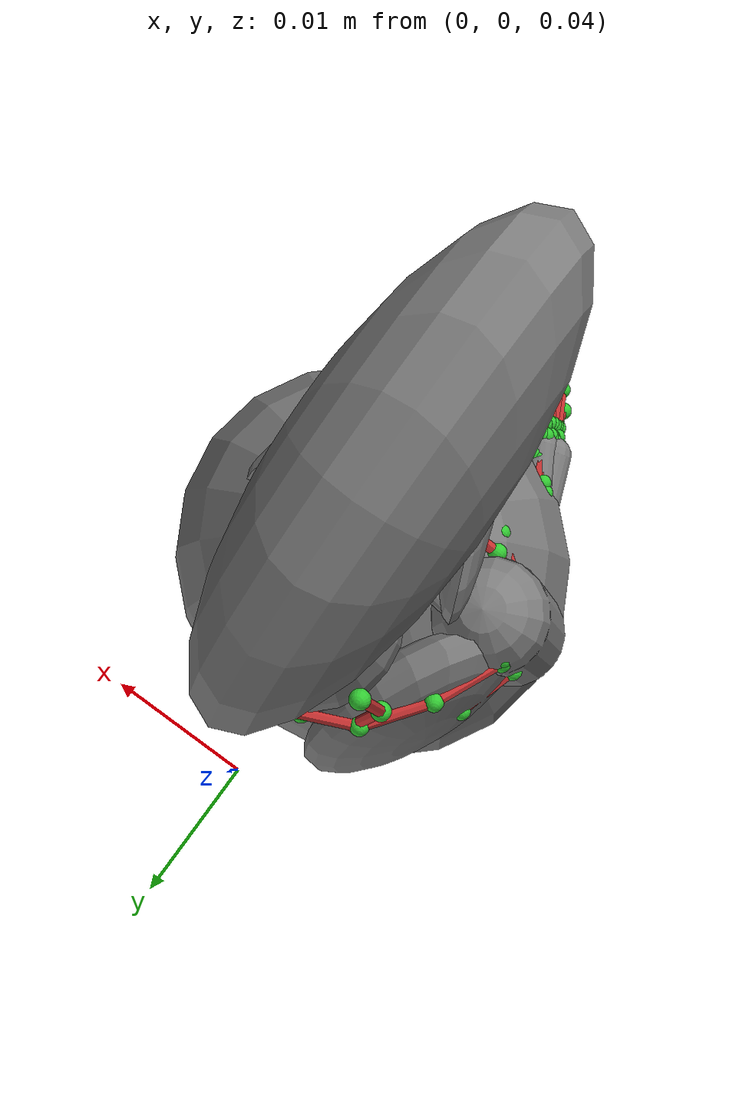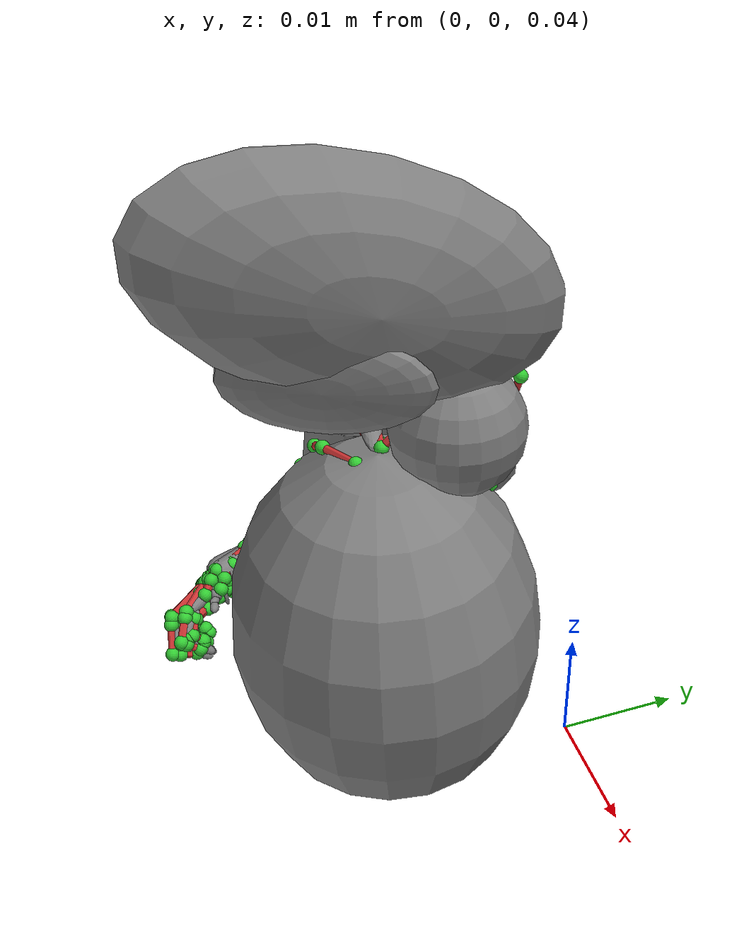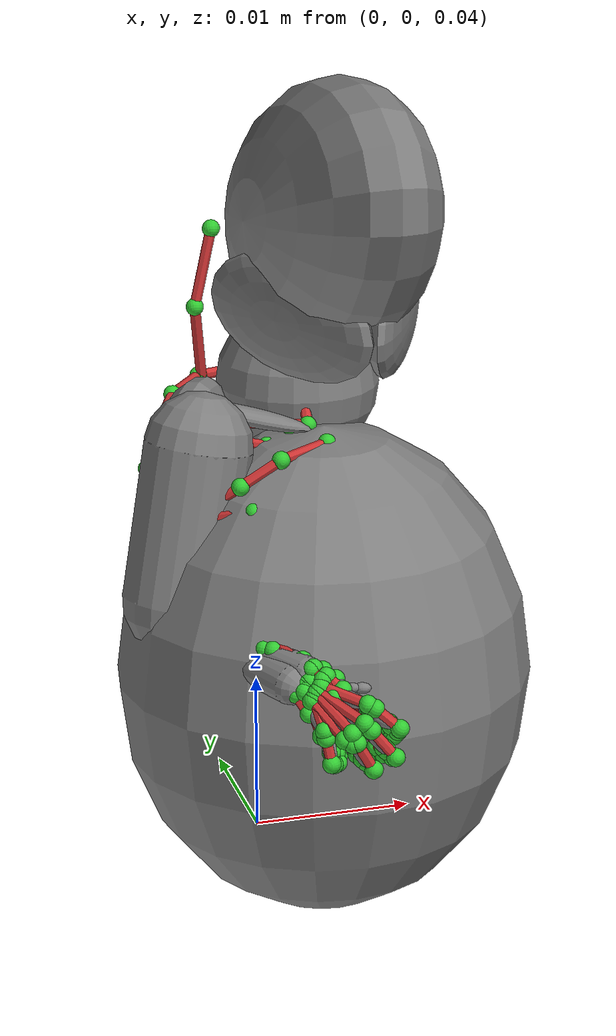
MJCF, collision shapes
<?xml version='1.0' encoding='utf-8'?>
<mujoco>
  <default>
    <site size="0.0005" rgba="0.2 0.8 0.2 1" />
    <tendon width="0.0003" rgba="0.8 0.2 0.2 1" />
    <joint damping="1e-5" solimplimit="0.0 0.95 0.035 0.5 2" solreflimit="0.002 1.0" />
    <muscle force=".5" group="0" timeconst="0.002 0.004" ctrllimited="true" ctrlrange="0 1" />
  </default>
  <visual>
    <headlight ambient="0.4 0.4 0.4" diffuse="0.6 0.6 0.6" specular="0.1 0.1 0.1" />
  </visual>
  <worldbody>
    <body name="Armature" pos="0.0 0.0 0.0" quat="1.0 0.0 0.0 0.0">
      <body name="T13" pos="5.6488395641817775e-18 -0.008783722296357155 0.04656617343425751" quat="0.7715498805046082 0.636168897151947 3.35192113052208e-17 -1.1368345498966205e-16">
        <body name="T12" pos="1.0339757656912846e-24 0.0024421592243015766 -9.313225746154785e-10" quat="0.998820424079895 0.04855736345052719 2.196913455654894e-17 -5.035747356227887e-18">
          <body name="T11" pos="-5.169878828456423e-26 0.002091360045596957 -9.313225746154785e-10" quat="0.9955549240112305 0.0941825658082962 -6.516475264389059e-17 -1.5163587130468935e-17">
            <body name="T10" pos="-1.8611563782443123e-24 0.0019373982213437557 2.3283064365386963e-10" quat="0.9995990991592407 0.028313929215073586 1.8619027984328324e-23 -6.286968047735811e-18">
              <body name="T9" pos="-8.271806125530277e-25 0.0018240385688841343 -2.9103830456733704e-11" quat="0.9985309839248657 0.05418374389410019 -1.7085699715758065e-24 -1.2031203870421491e-17">
                <body name="T8" pos="-4.1359030627651384e-25 0.0016756672412157059 -1.3969838619232178e-09" quat="0.9999998807907104 -0.0005197898135520518 1.5013876124993269e-18 1.270719923485213e-18">
                  <body name="T7" pos="2.0679515313825692e-24 0.0017587305046617985 4.656612873077393e-10" quat="0.9995011687278748 0.031581733375787735 -1.2919446542202877e-18 -7.932265854870123e-18">
                    <body name="T6" pos="1.4475660719677984e-24 0.0016421449836343527 0.0" quat="0.9998982548713684 0.01426623109728098 -7.154352326395906e-20 -3.2138595164081512e-18">
                      <body name="T5" pos="1.0339757656912846e-24 0.0016767673660069704 0.0" quat="0.9999992847442627 0.0011710383696481586 -1.8341419519080375e-19 -3.8805387074911233e-19">
                        <body name="T4" pos="4.1359030627651384e-25 0.001613495871424675 9.313225746154785e-10" quat="0.999898374080658 -0.014254982583224773 6.768663339168689e-19 3.6376499936132096e-18">
                          <body name="T3" pos="1.0339757656912846e-24 0.0015393148642033339 0.0" quat="0.9968907237052917 -0.07879666984081268 -6.300265079480177e-19 1.696302921757189e-17">
                            <body name="T2" pos="1.4475660719677984e-24 0.0015003972221165895 -1.7462298274040222e-10" quat="0.999866783618927 -0.016323154792189598 4.400823163571731e-19 3.997001239944009e-18">
                              <body name="scapula_right" pos="-0.004669216927140951 -0.0009179239859804511 -0.006343635730445385" quat="0.89564049243927 0.3798601031303406 0.1350710391998291 0.18785667419433594">
                                <body name="humerus_right" pos="1.1059455573558807e-09 0.010813232511281967 2.0954757928848267e-09" quat="0.37189534306526184 0.03516112640500069 0.4371594488620758 0.8181376457214355">
                                  <joint name="shoulder_protraction" type="hinge" limited="true" pos="0.0 0.0 0.0" axis="1.0 0.0 0.0" range="-45 45" />
                                  <joint name="shoulder_internal_rotation" type="hinge" limited="true" pos="0.0 0.0 0.0" axis="0.0 1.0 0.0" range="-45 45" />
                                  <joint name="shoulder_abduction" type="hinge" limited="true" pos="0.0 0.0 0.0" axis="0.0 0.0 1.0" range="-45 45" />
                                  <body name="ulna_right" pos="9.313225746154785e-10 0.010368258692324162 1.3969838619232178e-09" quat="0.7612545490264893 0.6444836854934692 -0.052472587674856186 -0.04877481982111931">
                                    <joint name="elbow_flexion" type="hinge" limited="true" pos="0.0 0.0 0.0" axis="1.0 0.0 0.0" range="-45 45" />
                                    <body name="radius_right" pos="0.0005716049927286804 6.419699639081955e-05 -0.00011007067223545164" quat="-0.992816150188446 -0.02420383132994175 -0.10135006159543991 -0.05880967155098915">
                                      <joint name="forearm_supination" type="hinge" limited="true" pos="0.0 0.0 0.0" axis="0.0 1.0 0.0" range="-45 45" />
                                      <body name="N_L_C_right" pos="9.313225746154785e-10 0.011701315641403198 -8.731149137020111e-10" quat="0.14538779854774475 0.422517329454422 0.7792569398880005 -0.43943166732788086">
                                        <joint name="wrist_deviation" type="hinge" limited="true" pos="0.0 0.0 0.0" axis="1.0 0.0 0.0" range="-45 45" />
                                        <joint name="wrist_flexion" type="hinge" limited="true" pos="0.0 0.0 0.0" axis="0.0 0.0 1.0" range="-45 45" />
                                        <body name="Metacarpal_hand_1_right" pos="0.0004065388347953558 -0.00037051388062536716 -0.0003569746622815728" quat="0.001941029098816216 -0.8046448826789856 -0.5621932148933411 0.19100159406661987">
                                          <joint name="mcp_flexion_1" type="hinge" limited="true" pos="0.0 0.0 0.0" axis="1.0 0.0 0.0" range="-5.0 5.0" />
                                          <joint name="mcp_abduction_1" type="hinge" limited="true" pos="0.0 0.0 0.0" axis="0.0 1.0 0.0" range="-5.0 5.0" />
                                          <body name="Phalanx_hand_1_1_right" pos="4.6566128730773926e-09 0.0006753515917807817 3.434251993894577e-09" quat="0.9412593245506287 0.25909313559532166 0.2048777937889099 -0.07019064575433731">
                                            <joint name="pip_flexion_1" type="hinge" limited="true" pos="0.0 0.0 0.0" axis="1.0 0.0 0.0" range="-5.0 5.0" />
                                            <body name="Phalanx_hand_2_1_right" pos="2.9103830456733704e-09 0.0006597413448616862 -6.693881005048752e-09" quat="0.9700450301170349 -0.22801397740840912 0.06510968506336212 0.052753981202840805">
                                              <joint name="dip_flexion_1" type="hinge" limited="true" pos="0.0 0.0 0.0" axis="1.0 0.0 0.0" range="-5.0 5.0" />
                                              <geom name="Phalanx_hand_2_1_right_bone" mesh="Phalanx_hand_2_1_right_bone" pos="-1.737498678267002e-08 -4.423782229423523e-09 9.762516128830612e-09" quat="0.5377950072288513 -0.30074450373649597 -0.394574910402298 0.6816450357437134" type="mesh" material="bone" contype="0" conaffinity="0" group="0" density="0" />
                                              <geom name="Phalanx_hand_2_1_right_col" type="ellipsoid" size="0.0004723376187030226 0.0003070329332234296 0.0002973566525041535" pos="-5.429997690953314e-05 0.00038592598866671324 -0.00010568481957307085" quat="0.42766979336738586 -0.5936122536659241 0.609771728515625 -0.3047974109649658" contype="1" conaffinity="0" group="1" />
                                            </body>
                                            <geom name="Phalanx_hand_1_1_right_bone" mesh="Phalanx_hand_1_1_right_bone" pos="-1.0069925338029861e-08 -1.1641532182693481e-10 1.3562384992837906e-08" quat="0.44284218549728394 -0.349165141582489 -0.2081812024116516 0.7991464734077454" type="mesh" material="bone" contype="0" conaffinity="0" group="0" density="0" />
                                            <geom name="Phalanx_hand_1_1_right_col" type="ellipsoid" size="0.0004890728164523989 0.0002894149565092381 0.0002865710854933201" pos="2.362125087529421e-05 0.00037310586776584387 -9.707867866382003e-05" quat="0.0007928490522317588 0.7602683305740356 -0.6438658237457275 -0.08618699759244919" contype="1" conaffinity="0" group="1" />
                                          </body>
                                          <geom name="Sesamoid_hand_b_right_bone" mesh="Sesamoid_hand_b_right_bone" pos="-9.509234223514795e-05 0.0006985135842114687 -0.0003126110532321036" quat="0.6060397028923035 -0.06480149179697037 -0.2877691984176636 0.7387188673019409" type="mesh" material="bone" contype="0" conaffinity="0" group="0" density="0" />
                                          <geom name="Multangular_right_bone" mesh="Multangular_right_bone" pos="-2.7939677238464355e-09 -1.0477378964424133e-08 7.683411240577698e-09" quat="0.6060397624969482 -0.0648014023900032 -0.2877688705921173 0.7387189269065857" type="mesh" material="bone" contype="0" conaffinity="0" group="0" density="0" />
                                          <geom name="Metacarpal_hand_1_right_bone" mesh="Metacarpal_hand_1_right_bone" pos="-5.9371814131736755e-09 -6.984919309616089e-09 1.8277205526828766e-08" quat="0.6060397028923035 -0.06480149179697037 -0.2877691984176636 0.7387188673019409" type="mesh" material="bone" contype="0" conaffinity="0" group="0" density="0" />
                                          <geom name="Metacarpal_hand_1_right_col" type="ellipsoid" size="0.00042687358650361426 0.0003952798017824669 0.0004364557513196962" pos="-1.5615893062204123e-05 0.00045968801714479923 -9.042967576533556e-05" quat="0.680575966835022 0.22539953887462616 -0.0028835791163146496 0.6971392035484314" contype="1" conaffinity="0" group="1" />
                                          <geom name="Multangular_right_col" type="ellipsoid" size="0.0003088218830117843 0.00024746794952079654 0.0002224578399218427" pos="7.25656864233315e-05 1.4963094145059586e-05 -1.5029043424874544e-05" quat="0.6896414756774902 -0.09425769746303558 0.7087329030036926 -0.11492528766393661" contype="1" conaffinity="0" group="1" />
                                          <geom name="Sesamoid_hand_b_right_col" type="ellipsoid" size="0.00028224807465448976 0.00018110145174432546 0.00011936548980884254" pos="-7.9834193456918e-05 0.000704567413777113 -0.00031446036882698536" quat="0.15466925501823425 -0.9549859166145325 0.09436117857694626 0.23489423096179962" contype="1" conaffinity="0" group="1" />
                                          <site name="epl_P6" pos="-0.00041542021790519357 0.00023593218065798283 -6.305432179942727e-05" />
                                          <site name="epb_P5" pos="-0.00041542021790519357 0.00023593218065798283 -6.305432179942727e-05" />
                                        </body>
                                        <body name="Metacarpal_hand_2_right" pos="0.0002825197298079729 -0.00012420862913131714 -0.0002580876462161541" quat="0.2168484628200531 -0.577779233455658 -0.7354013919830322 0.27987992763519287">
                                          <body name="Phalanx_hand_1_2_right" pos="-1.1641532182693481e-10 0.0025264841970056295 -1.6079866327345371e-09" quat="0.9702771306037903 -0.22301526367664337 0.01390919554978609 0.09291429817676544">
                                            <joint name="pip_flexion_2" type="hinge" limited="true" pos="0.0 0.0 0.0" axis="1.0 0.0 0.0" range="-5.0 5.0" />
                                            <body name="Phalanx_hand_2_2_right" pos="-1.1350493878126144e-09 0.0019351550145074725 -3.7071004044264555e-09" quat="0.6904518008232117 -0.7004584670066833 0.16852612793445587 0.06506338715553284">
                                              <joint name="dip_flexion_2" type="hinge" limited="true" pos="0.0 0.0 0.0" axis="1.0 0.0 0.0" range="-5.0 5.0" />
                                              <body name="Phalanx_hand_3_2_right" pos="1.4770193956792355e-09 0.0012717396020889282 3.536115400493145e-09" quat="0.9922130703926086 0.1244237869977951 0.0053625451400876045 0.0017839064821600914">
                                                <joint name="tip_flexion_2" type="hinge" limited="true" pos="0.0 0.0 0.0" axis="1.0 0.0 0.0" range="-5.0 5.0" />
                                                <geom name="Phalanx_hand_3_2_right_bone" mesh="Phalanx_hand_3_2_right_bone" pos="-7.3196133598685265e-09 -2.5756889954209328e-09 -2.510205376893282e-10" quat="0.3205825388431549 0.056336410343647 -0.8533391952514648 0.4072656035423279" type="mesh" material="bone" contype="0" conaffinity="0" group="0" density="0" />
                                                <geom name="Phalanx_hand_3_2_right_col" type="ellipsoid" size="0.0007001164485700428 0.00033376887927056426 0.00021890449289253128" pos="2.4586101062595844e-05 0.0004342776956036687 -1.7543545254739e-05" quat="0.45697641372680664 -0.5240138173103333 -0.4797261357307434 0.5352055430412292" contype="1" conaffinity="0" group="1" />
                                                <site name="Flexor_digitorum_profundus_SH_P6" pos="-3.6523299058899283e-05 -7.19297313480638e-05 -0.00033595593413338065" />
                                                <site name="Flexor_digitorum_profundus_SH_P7" pos="-1.4811987057328224e-05 1.5549270756309852e-05 -0.00022024581267032772" />
                                                <site name="edcA_P8" pos="1.0090609066537581e-05 7.463897782145068e-05 0.0002007984003284946" />
                                              </body>
                                              <geom name="Sesamoid_hand_n_right_bone" mesh="Sesamoid_hand_n_right_bone" pos="-5.666632205247879e-06 0.001233410439454019 -0.00027401986881159246" quat="0.3149246871471405 0.09949476271867752 -0.8955488204956055 0.29818832874298096" type="mesh" material="bone" contype="0" conaffinity="0" group="0" density="0" />
                                              <geom name="Phalanx_hand_2_2_right_bone" mesh="Phalanx_hand_2_2_right_bone" pos="7.792550604790449e-09 -5.6138560466933995e-09 1.1306838132441044e-08" quat="0.3149254322052002 0.09949177503585815 -0.895548403263092 0.2981887459754944" type="mesh" material="bone" contype="0" conaffinity="0" group="0" density="0" />
                                              <geom name="Phalanx_hand_2_2_right_col" type="ellipsoid" size="0.0009212680226915321 0.0002642836455923406 0.00030080823879528006" pos="4.9569018301554024e-05 0.0005441022804006934 -8.568500925321132e-05" quat="0.0362146720290184 -0.7081072330474854 0.7009227275848389 0.07733014225959778" contype="1" conaffinity="0" group="1" />
                                              <geom name="Sesamoid_hand_n_right_col" type="ellipsoid" size="0.00014268553059082478 0.00010731083602877334 7.019550685072318e-05" pos="-5.677196895703673e-06 0.0012334029888734221 -0.00027402484556660056" quat="0.082540363073349 -0.9867852926254272 0.13758057355880737 -0.022662479430437088" contype="1" conaffinity="0" group="1" />
                                              <site name="Flexor_digitorum_profundus_SH_P5" pos="-2.541043795645237e-05 0.00043365152669139206 -0.0004563888651318848" />
                                              <site name="fdsA_P7" pos="4.802460898645222e-05 0.000302097323583439 -0.00027193044661544263" />
                                              <site name="edcA_P7" pos="3.0166320357238874e-05 0.00024657155154272914 0.00019304048328194767" />
                                            </body>
                                            <geom name="Phalanx_hand_1_2_right_bone" mesh="Phalanx_hand_1_2_right_bone" pos="-2.7939677238464355e-09 -1.30385160446167e-08 -5.471520125865936e-09" quat="0.41865482926368713 -0.04337691515684128 -0.3499208390712738 0.8369002342224121" type="mesh" material="bone" contype="0" conaffinity="0" group="0" density="0" />
                                            <geom name="Phalanx_hand_1_2_right_col" type="ellipsoid" size="0.0012017625759375705 0.00040305747248482737 0.00039855595285100825" pos="4.0284241549670696e-05 0.0009321807301603258 -9.783290443010628e-05" quat="0.18915759027004242 0.6838018298149109 -0.6683969497680664 -0.2233382612466812" contype="1" conaffinity="0" group="1" />
                                            <site name="Flexor_digitorum_profundus_SH_P4" pos="-0.00012006517499685287 0.0002853667247109115 -0.00034155184403061867" />
                                            <site name="fdsA_P6" pos="-0.00012629717821255326 0.0002798183122649789 -0.00043384128366596997" />
                                            <site name="edcA_P5" pos="8.733151480555534e-05 0.00043549860129132867 0.00033384657581336796" />
                                            <site name="edcA_P6" pos="8.113535295706242e-05 0.00210944889113307 0.00014758067845832556" />
                                          </body>
                                          <geom name="Sesamoid_hand_j_right_bone" mesh="Sesamoid_hand_j_right_bone" pos="-0.0002882287371903658 0.0023140981793403625 -0.00021051664953120053" quat="0.3236443102359772 -0.09129955619573593 -0.15108492970466614 0.9295655488967896" type="mesh" material="bone" contype="0" conaffinity="0" group="0" density="0" />
                                          <geom name="Sesamoid_hand_i_right_bone" mesh="Sesamoid_hand_i_right_bone" pos="7.26417638361454e-05 0.002207194222137332 -0.000346843502484262" quat="0.3236443102359772 -0.09129955619573593 -0.15108492970466614 0.9295655488967896" type="mesh" material="bone" contype="0" conaffinity="0" group="0" density="0" />
                                          <geom name="Metacarpal_hand_2_right_bone" mesh="Metacarpal_hand_2_right_bone" pos="1.3969838619232178e-09 -3.259629011154175e-09 -6.417394615709782e-09" quat="0.3236444294452667 -0.09129957854747772 -0.15108464658260345 0.9295655488967896" type="mesh" material="bone" contype="0" conaffinity="0" group="0" density="0" />
                                          <geom name="Metacarpal_hand_2_right_col" type="ellipsoid" size="0.0015806542942300439 0.0004525682370708165 0.00042344955727458" pos="0.0001064968528226018 0.0012260102666914463 -7.521778752561659e-05" quat="0.36755508184432983 0.6170336604118347 -0.5355806946754456 -0.44421395659446716" contype="1" conaffinity="0" group="1" />
                                          <geom name="Sesamoid_hand_i_right_col" type="ellipsoid" size="0.00031377148116007447 0.00015244541282299906 0.0001483732194174081" pos="5.9313373640179634e-05 0.0022535002790391445 -0.00035552226472646" quat="0.19370004534721375 0.6282374262809753 -0.7533749341964722 -0.01493673026561737" contype="1" conaffinity="0" group="1" />
                                          <geom name="Sesamoid_hand_j_right_col" type="ellipsoid" size="0.00033533090027049184 0.00018532914691604674 0.0001690189092187211" pos="-0.0002787270350381732 0.002366719301789999 -0.00022314538364298642" quat="0.15493755042552948 -0.745619535446167 0.5683216452598572 -0.31153786182403564" contype="1" conaffinity="0" group="1" />
                                          <site name="fdsA_P5" pos="-0.00014448619913309813 0.0013797333231195807 -0.0007234637159854174" />
                                          <site name="extensorcarpiradialislongus_P4" pos="-8.214672561734915e-05 0.0009317165240645409 0.00014146007015369833" />
                                          <site name="edcA_P4" pos="0.0001207658788189292 0.00269136275164783 0.0002724366495385766" />
                                        </body>
                                        <body name="Metacarpal_hand_3_right" pos="0.0004491640720516443 0.0005535369273275137 -0.000305608962662518" quat="0.27782994508743286 -0.5320879817008972 -0.770694375038147 0.21382981538772583">
                                          <body name="Phalanx_hand_1_3_right" pos="-1.862645149230957e-09 0.002994047710672021 -1.076841726899147e-09" quat="0.9113362431526184 -0.3853777348995209 0.11947382986545563 0.08170801401138306">
                                            <joint name="pip_flexion_3" type="hinge" limited="true" pos="0.0 0.0 0.0" axis="1.0 0.0 0.0" range="-5.0 5.0" />
                                            <body name="Phalanx_hand_2_3_right" pos="-1.2514647096395493e-09 0.0021216454915702343 1.2369127944111824e-10" quat="0.6829180717468262 -0.7289460301399231 -0.01744973473250866 0.044227927923202515">
                                              <joint name="dip_flexion_3" type="hinge" limited="true" pos="0.0 0.0 0.0" axis="1.0 0.0 0.0" range="-5.0 5.0" />
                                              <body name="Phalanx_hand_3_3_right" pos="0.0 0.0014590825885534286 5.820766091346741e-11" quat="0.9649938344955444 0.2602379024028778 0.03198400139808655 -0.0063367923721671104">
                                                <joint name="tip_flexion_3" type="hinge" limited="true" pos="0.0 0.0 0.0" axis="1.0 0.0 0.0" range="-5.0 5.0" />
                                                <geom name="Phalanx_hand_3_3_right_bone" mesh="Phalanx_hand_3_3_right_bone" pos="1.0011717677116394e-08 -8.440110832452774e-10 1.8044374883174896e-09" quat="0.36212432384490967 0.013692876324057579 -0.8684067130088806 0.3384498953819275" type="mesh" material="bone" contype="0" conaffinity="0" group="0" density="0" />
                                                <geom name="Phalanx_hand_3_3_right_col" type="ellipsoid" size="0.0007360045700133475 0.00038062362000346184 0.00021192220063045476" pos="-3.013497916981578e-06 0.00047844331129454076 5.2151037380099297e-05" quat="0.5355066061019897 -0.4696522057056427 -0.4554412364959717 0.5340720415115356" contype="1" conaffinity="0" group="1" />
                                                <site name="Flexor_digitorum_profundus_RH_P7" pos="7.300637662410736e-06 -0.00011038180673494935 -0.00034330144990235567" />
                                                <site name="Flexor_digitorum_profundus_RH_P8" pos="2.491287887096405e-07 0.00021732285676989704 -0.0003111563855782151" />
                                                <site name="edcB_P8" pos="1.0876916348934174e-05 8.062379492912441e-05 0.0002177705755457282" />
                                              </body>
                                              <geom name="Phalanx_hand_2_3_right_bone" mesh="Phalanx_hand_2_3_right_bone" pos="6.111804395914078e-09 4.511093720793724e-10 5.122274160385132e-09" quat="0.37580400705337524 0.11277426034212112 -0.9145892262458801 0.09787677228450775" type="mesh" material="bone" contype="0" conaffinity="0" group="0" density="0" />
                                              <geom name="Sesamoid_hand_m_right_bone" mesh="Sesamoid_hand_m_right_bone" pos="-8.783536031842232e-08 0.0014927841257303953 -0.00022186909336596727" quat="0.37580400705337524 0.11277425289154053 -0.9145892262458801 0.09787680208683014" type="mesh" material="bone" contype="0" conaffinity="0" group="0" density="0" />
                                              <geom name="Phalanx_hand_2_3_right_col" type="ellipsoid" size="0.0009257117696189129 0.00031202269019559026 0.00031127239344641566" pos="1.1133553925901651e-05 0.0007062417571432889 -7.768173236399889e-05" quat="0.742036759853363 0.021185599267482758 -0.08609245717525482 0.6644703149795532" contype="1" conaffinity="0" group="1" />
                                              <geom name="Sesamoid_hand_m_right_col" type="ellipsoid" size="0.00018040102440863848 0.0001258305856026709 7.37344307708554e-05" pos="-9.231735020875931e-08 0.0014927831944078207 -0.0002218644949607551" quat="0.06503324955701828 0.020850230008363724 -0.9829123020172119 -0.17093674838542938" contype="1" conaffinity="0" group="1" />
                                              <site name="Flexor_digitorum_profundus_RH_P6" pos="-4.0228303987532854e-05 0.0003286107676103711 -0.0004830065299756825" />
                                              <site name="fdsB,_P7" pos="-1.0278774425387383e-05 0.0002733423316385597 -0.00028751330683007836" />
                                              <site name="edcB_P7" pos="4.138675285503268e-05 0.0002588890783954412 0.0002178299764636904" />
                                            </body>
                                            <geom name="Phalanx_hand_1_3_right_bone" mesh="Phalanx_hand_1_3_right_bone" pos="-5.820766091346741e-10 -1.7578713595867157e-08 2.954038791358471e-09" quat="0.31856241822242737 -0.1581815928220749 -0.5548154711723328 0.7521146535873413" type="mesh" material="bone" contype="0" conaffinity="0" group="0" density="0" />
                                            <geom name="Phalanx_hand_1_3_right_col" type="ellipsoid" size="0.0012912593102810607 0.0003662501694634557 0.00033117672453952633" pos="2.2149819415062666e-05 0.0010177417425438762 1.2079690350219607e-05" quat="0.05697768181562424 0.688938319683075 -0.7203633189201355 -0.056517984718084335" contype="1" conaffinity="0" group="1" />
                                            <site name="Flexor_digitorum_profundus_RH_P5" pos="1.4486722648143768e-06 0.0002649520756676793 -0.0003110680263489485" />
                                            <site name="fdsB,_P6" pos="-1.3498589396476746e-05 0.0002512743230909109 -0.0004527223645709455" />
                                            <site name="edcB_P5" pos="-5.840766243636608e-05 0.00027973297983407974 0.0003485409542918205" />
                                            <site name="edcB_P6" pos="3.807735629379749e-05 0.0022725467570126057 0.0002527199103496969" />
                                          </body>
                                          <geom name="Sesamoid_hand_h_right_bone" mesh="Sesamoid_hand_h_right_bone" pos="-0.0002393387258052826 0.0026463125832378864 -0.00015547947259619832" quat="0.23418956995010376 -0.13173097372055054 -0.19063879549503326 0.9441710710525513" type="mesh" material="bone" contype="0" conaffinity="0" group="0" density="0" />
                                          <geom name="Sesamoid_hand_g_right_bone" mesh="Sesamoid_hand_g_right_bone" pos="9.919027797877789e-05 0.002637838013470173 -0.00025866113719530404" quat="0.23418956995010376 -0.13173097372055054 -0.19063879549503326 0.9441710710525513" type="mesh" material="bone" contype="0" conaffinity="0" group="0" density="0" />
                                          <geom name="Metacarpal_hand_3_right_bone" mesh="Metacarpal_hand_3_right_bone" pos="2.3283064365386963e-10 -1.5133991837501526e-09 -2.444721758365631e-09" quat="0.23418962955474854 -0.13173124194145203 -0.1906386911869049 0.9441710710525513" type="mesh" material="bone" contype="0" conaffinity="0" group="0" density="0" />
                                          <geom name="Metacarpal_hand_3_right_col" type="ellipsoid" size="0.00179077860469945 0.00039994822471087904 0.0003831295242809774" pos="4.598591476678848e-05 0.0015024468302726746 5.5873359087854624e-05" quat="0.5486711859703064 0.4445313811302185 -0.4034237563610077 -0.5818943381309509" contype="1" conaffinity="0" group="1" />
                                          <geom name="Sesamoid_hand_g_right_col" type="ellipsoid" size="0.0003092387050855905 0.00016959277854766697 0.00013600068632513285" pos="0.00012514495756477118 0.0026757046580314636 -0.0002694439026527107" quat="0.22573617100715637 0.6453444957733154 -0.7244195342063904 -0.08825359493494034" contype="1" conaffinity="0" group="1" />
                                          <geom name="Sesamoid_hand_h_right_col" type="ellipsoid" size="0.00031314865918830037 0.00014781206846237183 0.00010825449862750247" pos="-0.00025494559668004513 0.002713883062824607 -0.000144079647725448" quat="0.6169880628585815 0.3989422619342804 -0.3991204798221588 -0.548517107963562" contype="1" conaffinity="0" group="1" />
                                          <site name="flexorcarpiradialis_P6" pos="-0.000153218861669302 0.00029495987109839916 -0.00027770770248025656" />
                                          <site name="fdsB,_P5" pos="-0.00025435909628868103 0.0009984391508623958 -0.000733568798750639" />
                                          <site name="extensororcarpiradialisbrevis_P4" pos="-0.00019471836276352406 0.0005719952750951052 0.0002624513872433454" />
                                          <site name="edcB_P4" pos="3.992789424955845e-05 0.003041844116523862 0.00037999125197529793" />
                                        </body>
                                        <body name="Metacarpal_hand_4_right" pos="0.00036356179043650627 0.0009604280348867178 -0.0002277831081300974" quat="0.476703405380249 -0.5126197934150696 -0.7140395045280457 0.011065858416259289">
                                          <body name="Phalanx_hand_1_4_right" pos="-1.7462298274040222e-09 0.0027383980341255665 -5.471520125865936e-09" quat="0.8843018412590027 -0.445399671792984 -0.12204325199127197 -0.06881020218133926">
                                            <joint name="pip_flexion_4" type="hinge" limited="true" pos="0.0 0.0 0.0" axis="1.0 0.0 0.0" range="-5.0 5.0" />
                                            <body name="Phalanx_hand_2_4_right" pos="8.149072527885437e-10 0.002102455822750926 2.473825588822365e-10" quat="0.7245980501174927 -0.6871868968009949 0.035348571836948395 0.03850078955292702">
                                              <joint name="dip_flexion_4" type="hinge" limited="true" pos="0.0 0.0 0.0" axis="1.0 0.0 0.0" range="-5.0 5.0" />
                                              <body name="Phalanx_hand_3_4_right" pos="5.820766091346741e-11 0.0014054153580218554 1.862645149230957e-09" quat="0.9227252006530762 0.34341615438461304 -0.15703389048576355 0.07735611498355865">
                                                <joint name="tip_flexion_4" type="hinge" limited="true" pos="0.0 0.0 0.0" axis="1.0 0.0 0.0" range="-5.0 5.0" />
                                                <geom name="Phalanx_hand_3_4_right_bone" mesh="Phalanx_hand_3_4_right_bone" pos="-4.001776687800884e-09 -1.7171259969472885e-08 5.820766091346741e-11" quat="0.3974566161632538 -0.16386623680591583 -0.8328204154968262 0.3486921787261963" type="mesh" material="bone" contype="0" conaffinity="0" group="0" density="0" />
                                                <geom name="Phalanx_hand_3_4_right_col" type="ellipsoid" size="0.000628135491444401 0.0003263379719771961 0.00020594950866204432" pos="1.1937518138438463e-06 0.0005346736870706081 -1.2350734323263168e-05" quat="0.44451966881752014 0.5489124059677124 -0.5144469141960144 -0.48625263571739197" contype="1" conaffinity="0" group="1" />
                                                <site name="flexor_digitorum_profundus_UH_P7" pos="2.5911045668181032e-05 -0.00019355874974280596 -0.00031947868410497904" />
                                                <site name="flexor_digitorum_profundus_UH_P8" pos="1.3098942872602493e-05 0.0001665755407884717 -0.0003026524791494012" />
                                                <site name="edcC_P8" pos="-1.224615698447451e-05 0.00011855177581310272 0.00022081012139096856" />
                                              </body>
                                              <geom name="Phalanx_hand_2_4_right_bone" mesh="Phalanx_hand_2_4_right_bone" pos="1.7171259969472885e-09 -1.2219970813021064e-08 -2.3865140974521637e-09" quat="0.2652638256549835 -0.005043393932282925 -0.963300883769989 0.040756773203611374" type="mesh" material="bone" contype="0" conaffinity="0" group="0" density="0" />
                                              <geom name="Sesamoid_hand_l_right_bone" mesh="Sesamoid_hand_l_right_bone" pos="9.276796481572092e-05 0.0015519600128754973 -0.00019671267364174128" quat="0.2652621865272522 -0.005041389726102352 -0.963301420211792 0.040755338966846466" type="mesh" material="bone" contype="0" conaffinity="0" group="0" density="0" />
                                              <geom name="Phalanx_hand_2_4_right_col" type="ellipsoid" size="0.000981289543015712 0.0003139253842889475 0.0003432182798013359" pos="-5.779613275080919e-06 0.0006126913940533996 -8.053984493017197e-05" quat="0.11076237261295319 -0.7177107334136963 0.6870591640472412 -0.023932674899697304" contype="1" conaffinity="0" group="1" />
                                              <geom name="Sesamoid_hand_l_right_col" type="ellipsoid" size="0.00017351853603031486 0.00012491580855567008 6.60749283269979e-05" pos="0.00011811195872724056 0.0015705933328717947 -0.0001867710379883647" quat="0.2760958671569824 -0.9427101612091064 -0.07765424996614456 -0.17040669918060303" contype="1" conaffinity="0" group="1" />
                                              <site name="flexor_digitorum_profundus_UH_P6" pos="8.6994405137375e-05 0.0003386964090168476 -0.0004774980479851365" />
                                              <site name="fdsC_P7" pos="7.1056128945201635e-06 0.0002382817183388397 -0.0002673174603842199" />
                                              <site name="edcC_P7" pos="-6.747301085852087e-05 0.00019605601846706122 0.00023133191280066967" />
                                            </body>
                                            <geom name="Phalanx_hand_1_4_right_bone" mesh="Phalanx_hand_1_4_right_bone" pos="4.190951585769653e-09 -1.076841726899147e-08 -6.548361852765083e-10" quat="0.22122716903686523 -0.14741142094135284 -0.6608186364173889 0.7018882632255554" type="mesh" material="bone" contype="0" conaffinity="0" group="0" density="0" />
                                            <geom name="Phalanx_hand_1_4_right_col" type="ellipsoid" size="0.001157564042057746 0.0003718025400303304 0.00032958772426391544" pos="3.84659506380558e-06 0.0012366119772195816 1.786230131983757e-05" quat="0.02108827233314514 0.7180094122886658 -0.6954767107963562 -0.01816401816904545" contype="1" conaffinity="0" group="1" />
                                            <site name="flexor_digitorum_profundus_UH_P5" pos="1.1452706530690193e-05 0.0003298877854831517 -0.0002756993053480983" />
                                            <site name="fdsC_P6" pos="-4.889443516731262e-06 0.00039861409459263086 -0.00026293989503756166" />
                                            <site name="extensordigitiquatri_P5" pos="0.00011789239943027496 0.0003033095272257924 0.0002636421122588217" />
                                            <site name="edcC_P5" pos="-7.983180694282055e-05 0.0003497540019452572 0.000349195150192827" />
                                            <site name="edcC_P6" pos="-7.221067789942026e-05 0.0022507004905492067 0.00020463074906729162" />
                                          </body>
                                          <geom name="Sesamoid_hand_f_right_bone" mesh="Sesamoid_hand_f_right_bone" pos="-0.00010717264376580715 0.002360055223107338 -0.0002655588323250413" quat="0.09762342274188995 -0.3600209057331085 -0.28859731554985046 0.881797194480896" type="mesh" material="bone" contype="0" conaffinity="0" group="0" density="0" />
                                          <geom name="Sesamoid_hand_e_right_bone" mesh="Sesamoid_hand_e_right_bone" pos="0.0002648482332006097 0.0023842707742005587 -0.0001514070900157094" quat="0.09762342274188995 -0.3600209057331085 -0.28859731554985046 0.881797194480896" type="mesh" material="bone" contype="0" conaffinity="0" group="0" density="0" />
                                          <geom name="Sesamoid_hand_a_right_bone" mesh="Sesamoid_hand_a_right_bone" pos="0.00010335707338526845 9.247346315532923e-05 -0.000514528714120388" quat="0.09762342274188995 -0.3600209057331085 -0.28859731554985046 0.881797194480896" type="mesh" material="bone" contype="0" conaffinity="0" group="0" density="0" />
                                          <geom name="Metacarpal_hand_4_right_bone" mesh="Metacarpal_hand_4_right_bone" pos="1.1641532182693481e-09 -2.2118911147117615e-09 -4.190951585769653e-09" quat="0.09762366861104965 -0.3600209355354309 -0.28859707713127136 0.881797194480896" type="mesh" material="bone" contype="0" conaffinity="0" group="0" density="0" />
                                          <geom name="Metacarpal_hand_4_right_col" type="ellipsoid" size="0.001748770708218217 0.0003569774697004917 0.0003660670626969807" pos="-1.5988829545676708e-05 0.001551798195578158 4.069879651069641e-05" quat="0.22065873444080353 -0.6817464232444763 0.6809173226356506 -0.15127183496952057" contype="1" conaffinity="0" group="1" />
                                          <geom name="Sesamoid_hand_a_right_col" type="ellipsoid" size="0.0002717851020861417 0.00016667410091031343 9.293900075135753e-05" pos="0.0001344872871413827 5.636061541736126e-05 -0.0005181042943149805" quat="0.08273156732320786 -0.9305413365364075 0.3514679968357086 -0.06097929924726486" contype="1" conaffinity="0" group="1" />
                                          <geom name="Sesamoid_hand_e_right_col" type="ellipsoid" size="0.00032886676490306854 0.00015652482397854328 0.00012442500155884773" pos="0.000274197431281209 0.002433938905596733 -0.00014898693189024925" quat="0.43480992317199707 0.544857382774353 -0.5529264807701111 -0.4564485549926758" contype="1" conaffinity="0" group="1" />
                                          <geom name="Sesamoid_hand_f_right_col" type="ellipsoid" size="0.0003217674093320966 0.00015718824579380453 0.00013718147238250822" pos="-0.00012271851301193237 0.002397203352302313 -0.0002887693699449301" quat="0.10266119986772537 -0.7127342820167542 0.63322514295578 -0.28372111916542053" contype="1" conaffinity="0" group="1" />
                                          <site name="fdsC_P5" pos="0.0001320124138146639 0.0009281833190470934 -0.0008267229422926903" />
                                          <site name="extensordigitiquatri_P4" pos="0.0003010309301316738 0.0027089696377515793 0.00018393038772046566" />
                                          <site name="edcC_P4" pos="-0.0002418516669422388 0.0028290138579905033 0.00030842586420476437" />
                                        </body>
                                        <body name="Metacarpal_hand_5_right" pos="0.0004799508024007082 0.0011933217756450176 0.00031333265360444784" quat="0.40877407789230347 -0.44122371077537537 -0.7979141473770142 0.039476945996284485">
                                          <body name="Phalanx_hand_1_5_right" pos="-4.656612873077393e-10 0.0015071533853188157 8.381903171539307e-09" quat="0.8920979499816895 -0.2958472967147827 0.21937765181064606 -0.26174235343933105">
                                            <joint name="pip_flexion_5" type="hinge" limited="true" pos="0.0 0.0 0.0" axis="1.0 0.0 0.0" range="-5.0 5.0" />
                                            <body name="Phalanx_hand_2_5_right" pos="2.0954757928848267e-09 0.0016548914136365056 -1.862645149230957e-09" quat="0.7701439261436462 -0.626035213470459 -0.11916721612215042 -0.02752106823027134">
                                              <joint name="dip_flexion_5" type="hinge" limited="true" pos="0.0 0.0 0.0" axis="1.0 0.0 0.0" range="-5.0 5.0" />
                                              <body name="Phalanx_hand_3_5_right" pos="6.984919309616089e-10 0.0009781959233805537 -2.0081643015146255e-09" quat="0.9202202558517456 0.38006043434143066 0.0036208888050168753 -0.09346479922533035">
                                                <joint name="tip_flexion_5" type="hinge" limited="true" pos="0.0 0.0 0.0" axis="1.0 0.0 0.0" range="-5.0 5.0" />
                                                <geom name="Phalanx_hand_3_5_right_bone" mesh="Phalanx_hand_3_5_right_bone" pos="-1.862645149230957e-09 -1.0419171303510666e-08 -2.3283064365386963e-10" quat="0.019678175449371338 0.20763325691223145 0.8132184147834778 -0.543302059173584" type="mesh" material="bone" contype="0" conaffinity="0" group="0" density="0" />
                                                <geom name="Phalanx_hand_3_5_right_col" type="ellipsoid" size="0.000521581352088938 0.00033491074487430016 0.00019672767666634172" pos="-1.4011748135089874e-06 0.00037384132156148553 2.048444002866745e-05" quat="0.5387392044067383 -0.45098206400871277 0.5056260824203491 -0.5007171630859375" contype="1" conaffinity="0" group="1" />
                                                <site name="flexor_digitorum_profundus_MH_P6" pos="5.264324136078358e-05 -0.0001870398409664631 -0.0002455908106639981" />
                                                <site name="flexor_digitorum_profundus_MH_P7" pos="1.5986617654561996e-05 0.00019294756930321455 -0.000320945808198303" />
                                                <site name="edcD_P8" pos="1.2729782611131668e-05 9.834527736529708e-05 0.00017190480139106512" />
                                              </body>
                                              <geom name="Sesamoid_hand_k_right_bone" mesh="Sesamoid_hand_k_right_bone" pos="2.6431400328874588e-05 0.0010159250814467669 -0.00021844470757059753" quat="0.11452783644199371 -0.2725846469402313 -0.935492992401123 0.19347773492336273" type="mesh" material="bone" contype="0" conaffinity="0" group="0" density="0" />
                                              <geom name="Phalanx_hand_2_5_right_bone" mesh="Phalanx_hand_2_5_right_bone" pos="9.313225746154785e-10 -1.4901161193847656e-08 -1.4551915228366852e-09" quat="0.11452791839838028 -0.2725869417190552 -0.9354920983314514 0.193479523062706" type="mesh" material="bone" contype="0" conaffinity="0" group="0" density="0" />
                                              <geom name="Phalanx_hand_2_5_right_col" type="ellipsoid" size="0.0005524506406603402 0.0003099389829802363 0.0002565402231764491" pos="4.963250830769539e-06 0.0005881472025066614 -1.1439755326136947e-05" quat="0.7086368203163147 0.13491596281528473 -0.1116219237446785 -0.6834998726844788" contype="1" conaffinity="0" group="1" />
                                              <geom name="Sesamoid_hand_k_right_col" type="ellipsoid" size="0.00015370936307590455 0.00010983058746205643 7.157840445870534e-05" pos="2.6423949748277664e-05 0.0010159157682210207 -0.00021844750153832138" quat="0.2320018708705902 -0.928462564945221 0.2780427932739258 -0.08261208236217499" contype="1" conaffinity="0" group="1" />
                                              <site name="flexor_digitorum_profundus_MH_P5" pos="2.752663567662239e-05 0.00027286901604384184 -0.0004355298588052392" />
                                              <site name="edcD_P7" pos="7.018912583589554e-06 0.00019852828700095415 0.00021745823323726654" />
                                            </body>
                                            <geom name="Phalanx_hand_1_5_right_bone" mesh="Phalanx_hand_1_5_right_bone" pos="2.561137080192566e-09 5.413312464952469e-09 -4.190951585769653e-09" quat="0.18860073387622833 0.330432653427124 0.6054871678352356 -0.699020266532898" type="mesh" material="bone" contype="0" conaffinity="0" group="0" density="0" />
                                            <geom name="Phalanx_hand_1_5_right_col" type="ellipsoid" size="0.0008796264767573919 0.0003912551037501544 0.00033505138537857915" pos="3.873556852340698e-05 0.0009799362160265446 -1.814751885831356e-05" quat="0.07172410935163498 -0.7220248579978943 0.6881268620491028 -0.004154071677476168" contype="1" conaffinity="0" group="1" />
                                            <site name="flexor_digitorum_profundus_MH_P4" pos="0.00017110956832766533 0.00024361861869692802 -0.0003745888825505972" />
                                            <site name="edcD_P5" pos="-7.900013588368893e-05 0.00033238588366657495 0.00027345609851181507" />
                                            <site name="edcD_P6" pos="-6.621680222451687e-05 0.0017666500061750412 0.00018384354189038277" />
                                            <site name="Abductor_digiti_quinti_hand_P1" pos="0.0004071767907589674 0.0003109051613137126 -0.00014097429811954498" />
                                          </body>
                                          <geom name="Sesamoid_hand_d_right_bone" mesh="Sesamoid_hand_d_right_bone" pos="-0.00014305219519883394 0.0012178984470665455 -0.00017737643793225288" quat="0.04978696629405022 -0.24411140382289886 -0.2882367670536041 0.9245812296867371" type="mesh" material="bone" contype="0" conaffinity="0" group="0" density="0" />
                                          <geom name="Sesamoid_hand_c_right_bone" mesh="Sesamoid_hand_c_right_bone" pos="0.00019097095355391502 0.0011627937201410532 -0.00026986596640199423" quat="0.04978696629405022 -0.24411140382289886 -0.2882367670536041 0.9245812296867371" type="mesh" material="bone" contype="0" conaffinity="0" group="0" density="0" />
                                          <geom name="Metacarpal_hand_5_right_bone" mesh="Metacarpal_hand_5_right_bone_bone" pos="5.704350769519806e-09 2.6193447411060333e-09 1.1059455573558807e-08" quat="0.04978714883327484 -0.24411141872406006 -0.2882365584373474 0.9245812892913818" type="mesh" material="bone" contype="0" conaffinity="0" group="0" density="0" />
                                          <geom name="Metacarpal_hand_5_right_col" type="ellipsoid" size="0.0011632201965468963 0.00037903295014984906 0.00036463794803586955" pos="7.810129318386316e-05 0.0008824475225992501 4.6036322601139545e-05" quat="0.3277357816696167 0.6236866116523743 -0.6304519772529602 -0.32578298449516296" contype="1" conaffinity="0" group="1" />
                                          <geom name="Sesamoid_hand_c_right_col" type="ellipsoid" size="0.0002732257707975805 0.0001920243084896356 0.00014551632921211421" pos="0.00018220394849777222 0.0011774444719776511 -0.000322784180752933" quat="0.16787837445735931 -0.7059206962585449 0.5521264672279358 -0.41066914796829224" contype="1" conaffinity="0" group="1" />
                                          <geom name="Sesamoid_hand_d_right_col" type="ellipsoid" size="0.0002369286521570757 0.00017235179257113487 0.00015111705579329282" pos="-0.0001213013892993331 0.001244842540472746 -0.00017640087753534317" quat="0.47580596804618835 0.6131554841995239 -0.5972514748573303 -0.2023477852344513" contype="1" conaffinity="0" group="1" />
                                          <site name="extensorcarpiiulnaris_P3" pos="0.000306601170450449 0.00010384072083979845 -5.477841477841139e-05" />
                                          <site name="edcD_P4" pos="6.902054883539677e-05 0.0016386797651648521 0.0003121031913906336" />
                                        </body>
                                        <geom name="Triangular_right_bone" mesh="Triangular_right_bone" pos="-0.0003802953287959099 0.000810073921456933 0.0003412598744034767" quat="0.353843092918396 0.8481107354164124 -0.24076302349567413 -0.31230831146240234" type="mesh" material="bone" contype="0" conaffinity="0" group="0" density="0" />
                                        <geom name="Pisiform_right_bone" mesh="Pisiform_right_bone" pos="-0.0003802953287959099 0.000810073921456933 0.0003412598744034767" quat="0.353843092918396 0.8481107354164124 -0.24076302349567413 -0.31230831146240234" type="mesh" material="bone" contype="0" conaffinity="0" group="0" density="0" />
                                        <geom name="Navicular_lunate_right_bone" mesh="Navicular_lunate_right_bone" pos="-0.0003802953287959099 0.000810073921456933 0.0003412598744034767" quat="0.353843092918396 0.8481107354164124 -0.24076302349567413 -0.31230831146240234" type="mesh" material="bone" contype="0" conaffinity="0" group="0" density="0" />
                                        <geom name="Hamate_right_bone" mesh="Hamate_right_bone" pos="-0.0003802953287959099 0.000810073921456933 0.0003412598744034767" quat="0.353843092918396 0.8481107354164124 -0.24076302349567413 -0.31230831146240234" type="mesh" material="bone" contype="0" conaffinity="0" group="0" density="0" />
                                        <geom name="Falsiformis_right_bone" mesh="Falsiformis_right_bone" pos="-0.0003802953287959099 0.000810073921456933 0.0003412598744034767" quat="0.353843092918396 0.8481107354164124 -0.24076302349567413 -0.31230831146240234" type="mesh" material="bone" contype="0" conaffinity="0" group="0" density="0" />
                                        <geom name="Centrale_right_bone" mesh="Centrale_right_bone" pos="-0.0003802953287959099 0.000810073921456933 0.0003412598744034767" quat="0.353843092918396 0.8481107354164124 -0.24076302349567413 -0.31230831146240234" type="mesh" material="bone" contype="0" conaffinity="0" group="0" density="0" />
                                        <geom name="Capitate_right_bone" mesh="Capitate_right_bone" pos="-0.0003802953287959099 0.000810073921456933 0.0003412598744034767" quat="0.353843092918396 0.8481107354164124 -0.24076302349567413 -0.31230831146240234" type="mesh" material="bone" contype="0" conaffinity="0" group="0" density="0" />
                                        <geom name="Capitate_right_col" type="ellipsoid" size="0.00043159346289744355 0.00027813212437872645 0.0003330964915729418" pos="0.00011332053691148758 0.00043739378452301025 -0.0001642454881221056" quat="0.1440650373697281 -0.34502601623535156 0.20520639419555664 0.904484748840332" contype="1" conaffinity="0" group="1" />
                                        <geom name="Centrale_right_col" type="ellipsoid" size="0.00040196315249097295 0.000333645150155798 0.00015634482840042561" pos="0.00014722743071615696 5.789753049612045e-05 -0.0002170155057683587" quat="0.31908726692199707 -0.18404355645179749 -0.47482815384864807 0.7992806434631348" contype="1" conaffinity="0" group="1" />
                                        <geom name="Falsiformis_right_col" type="ellipsoid" size="0.0008822327059055529 0.0003524172741740123 0.00017914276678884095" pos="0.0008809349965304136 -0.0004411204718053341 0.000490794307552278" quat="0.8759335279464722 0.23272056877613068 -0.2873495817184448 0.3098577558994293" contype="1" conaffinity="0" group="1" />
                                        <geom name="Hamate_right_col" type="ellipsoid" size="0.0005550822917126247 0.00035245631388552967 0.00029014749452471733" pos="0.00018586660735309124 0.0008974582888185978 0.00015377893578261137" quat="0.001709582982584834 0.7789673209190369 0.5266167521476746 0.34041425585746765" contype="1" conaffinity="0" group="1" />
                                        <geom name="Navicular_lunate_right_col" type="ellipsoid" size="0.0007837002066744987 0.0005535501809453107 0.00042048250907100737" pos="0.0002297458704560995 -4.610605537891388e-05 0.00012871623039245605" quat="0.4281717538833618 -0.1286843866109848 -0.24640299379825592 0.8598807454109192" contype="1" conaffinity="0" group="1" />
                                        <geom name="Pisiform_right_col" type="ellipsoid" size="0.0005648015066981316 0.00038427120307460427 0.0003945605712942779" pos="3.2865675166249275e-05 0.00047325482591986656 0.0009732461767271161" quat="0.23534496128559113 -0.539776086807251 -0.1000983864068985 0.8020195960998535" contype="1" conaffinity="0" group="1" />
                                        <geom name="Triangular_right_col" type="ellipsoid" size="0.00043076969282311584 0.0003334793456300743 0.0002056218164034852" pos="-4.382221959531307e-05 0.0007932311855256557 0.0003795623779296875" quat="0.3190799653530121 0.31977325677871704 -0.1943703442811966 -0.8707199692726135" contype="1" conaffinity="0" group="1" />
                                        <site name="palmarislongus_P4" pos="0.0005172069650143385 -0.00024623144418001175 0.0013873073039576411" />
                                        <site name="flexorcarpiradialis_P5" pos="0.00044261268340051174 -0.00010718568228185177 0.00014988204929977655" />
                                        <site name="flexorcarpiiulnaris_P2" pos="0.00014522508718073368 0.00025650556199252605 0.0014063261914998293" />
                                        <site name="flexor_digitorum_profundus_UH_P4" pos="0.000870843417942524 0.0006418663542717695 0.00028987356927245855" />
                                        <site name="Flexor_digitorum_profundus_SH_P3" pos="0.0009802136337384582 -0.00010025780647993088 0.00021845719311386347" />
                                        <site name="Flexor_digitorum_profundus_RH_P4" pos="0.000888788839802146 0.0003195826429873705 0.00022274407092481852" />
                                        <site name="flexor_digitorum_profundus_MH_P3" pos="0.0008706774096935987 0.000741621945053339 0.000545228598639369" />
                                        <site name="fdsD_P3" pos="0.00016319588758051395 -0.0001249159686267376 0.0015775163192301989" />
                                        <site name="fdsC_P4" pos="0.0007497316692024469 0.0004041185602545738 0.0005917138187214732" />
                                        <site name="fdsB,_P4" pos="0.0007729623466730118 0.0002121992874890566 0.00048528925981372595" />
                                        <site name="fdsA_P4" pos="0.000939240213483572 -5.138700362294912e-05 0.0004078532801941037" />
                                        <site name="extensororcarpiradialisbrevis_P3" pos="-0.00018528406508266926 2.2389227524399757e-05 -0.0005471569020301104" />
                                        <site name="extensordigitiquatri_P3" pos="3.0543655157089233e-05 0.0011726019438356161 -0.0001276575494557619" />
                                        <site name="extensorcarpiradialislongus_P3" pos="-0.00013714097440242767 -0.00027018552646040916 -0.0005979518173262477" />
                                        <site name="edcD_P3" pos="-1.1324882507324219e-06 0.0009867572225630283 -0.00022076768800616264" />
                                        <site name="edcC_P3" pos="-5.0511909648776054e-05 0.0007851002737879753 -0.0003309563035145402" />
                                        <site name="edcB_P3" pos="-4.2642466723918915e-05 0.0006604099180549383 -0.00041077553760260344" />
                                        <site name="edcA_P3" pos="-7.301918230950832e-05 0.0003760731779038906 -0.0005324793746694922" />
                                        <site name="Abductor_digiti_quinti_hand_P0" pos="0.00047894823364913464 0.000522552290931344 0.001204639091156423" />
                                      </body>
                                      <geom name="Sesamoid_elbow_right_bone" mesh="Sesamoid_elbow_right_bone" pos="0.0006637983024120331 0.0004993875045329332 0.00020064308773726225" quat="0.2546878159046173 0.06784351170063019 1.1411746072553797e-06 0.9646405577659607" type="mesh" material="bone" contype="0" conaffinity="0" group="0" density="0" />
                                      <geom name="radius_right_bone" mesh="radius_right_bone" pos="-0.0005377219058573246 4.612607881426811e-06 3.185041714459658e-05" quat="0.25468772649765015 0.06784358620643616 8.273998446384212e-07 0.9646406173706055" type="mesh" material="bone" contype="0" conaffinity="0" group="0" density="0" />
                                      <geom name="radius_right_col" type="capsule" size="0.0009157677995972335 0.004743554165136471" pos="0.00012067100033164024 0.006084193475544453 0.0003441360895521939" quat="0.6352471709251404 0.6368908286094666 -0.3129344582557678 0.3048003315925598" contype="1" conaffinity="0" group="1" />
                                      <site name="palmarislongus_P1" pos="-0.0020110122859477997 0.002440075622871518 -0.000555909879039973" />
                                      <site name="palmarislongus_P2" pos="-0.001149758230894804 0.0049536945298314095 -0.0008085669833235443" />
                                      <site name="palmarislongus_P3" pos="-0.0005338364280760288 0.008021664805710316 -0.0006368241156451404" />
                                      <site name="flexorcarpiradialis_P1" pos="-0.0016745147295296192 0.0030979968141764402 0.0006325198337435722" />
                                      <site name="flexorcarpiradialis_P2" pos="-0.0005422066897153854 0.006649843417108059 0.0006105484208092093" />
                                      <site name="flexorcarpiradialis_P3" pos="-0.0001215646043419838 0.00890370924025774 0.00044648884795606136" />
                                      <site name="flexorcarpiradialis_P4" pos="-0.00039726169779896736 0.011011729016900063 -7.135589839890599e-05" />
                                      <site name="flexor_digitorum_profundus_UH_P2" pos="-0.00029675522819161415 0.008103517815470695 -5.39464526809752e-05" />
                                      <site name="Flexor_digitorum_profundus_SH_P1" pos="-0.0006736959330737591 0.006349906325340271 -0.00010859192116186023" />
                                      <site name="Flexor_digitorum_profundus_SH_P2" pos="-0.0006232785526663065 0.01126445084810257 -0.0004728678904939443" />
                                      <site name="Flexor_digitorum_profundus_RH_P0" pos="-0.00026581529527902603 0.0022687334567308426 0.000342830375302583" />
                                      <site name="Flexor_digitorum_profundus_RH_P1" pos="-0.00024212803691625595 0.005367466248571873 0.0003711537574417889" />
                                      <site name="Flexor_digitorum_profundus_RH_P2" pos="-0.00015482120215892792 0.008721083402633667 -0.00011329806875437498" />
                                      <site name="Flexor_digitorum_profundus_RH_P3" pos="-0.00040870439261198044 0.01123477891087532 -0.0004981377278454602" />
                                      <site name="pronatorteres_P1" pos="5.2834395319223404e-05 0.005452906712889671 0.0010511919390410185" />
                                      <site name="fdsD_P1" pos="-0.00012906640768051147 0.005810298956930637 -0.0008351784781552851" />
                                      <site name="fdsD_P2" pos="-7.173861376941204e-05 0.01003942359238863 -0.000823682639747858" />
                                      <site name="fdsC_P1" pos="-0.000596342608332634 0.005322150886058807 -0.0004825795767828822" />
                                      <site name="fdsC_P2" pos="-0.00018001766875386238 0.00943627581000328 -0.0006573487771674991" />
                                      <site name="fdsC_P3" pos="-0.0002706653904169798 0.011098532937467098 -0.000837031053379178" />
                                      <site name="fdsB,_P1" pos="-0.000596342608332634 0.005322150886058807 -0.0004825795767828822" />
                                      <site name="fdsB,_P2" pos="-0.00032763974741101265 0.009466144256293774 -0.0006459252326749265" />
                                      <site name="fdsB,_P3" pos="-0.00036789290606975555 0.011137071065604687 -0.0007531404262408614" />
                                      <site name="fdsA_P1" pos="-0.000596342608332634 0.005322150886058807 -0.0004825795767828822" />
                                      <site name="fdsA_P2" pos="-0.00041522085666656494 0.009449908509850502 -0.000398311298340559" />
                                      <site name="fdsA_P3" pos="-0.0005515215452760458 0.011185264214873314 -0.0006239796639420092" />
                                      <site name="extensororcarpiradialisbrevis_P1" pos="0.00036801770329475403 0.00522061251103878 0.0012824537698179483" />
                                      <site name="extensororcarpiradialisbrevis_P2" pos="0.0003537684679031372 0.011298748664557934 0.0007629534811712801" />
                                      <site name="extensorcarpiradialislongus_P1" pos="0.00021187961101531982 0.005479182116687298 0.001418037456460297" />
                                      <site name="extensorcarpiradialislongus_P2" pos="0.00020568002946674824 0.011304658837616444 0.0008373919408768415" />
                                      <site name="epl_P1" pos="0.00040563615038990974 0.0029669185169041157 -0.00045167020289227366" />
                                      <site name="epl_P2" pos="0.000779071357101202 0.006697334814816713 0.00044924288522452116" />
                                      <site name="epl_P3" pos="0.000616616103798151 0.008006363175809383 0.000918353907763958" />
                                      <site name="epl_P4" pos="0.00012451549991965294 0.010105450637638569 0.0008018383523449302" />
                                      <site name="epl_P5" pos="-0.0005476288497447968 0.011296086013317108 0.0005965292220935225" />
                                      <site name="epb_P0" pos="0.0003580464981496334 0.0021111867390573025 0.00010109826689586043" />
                                      <site name="epb_P1" pos="0.0007165111601352692 0.006671795155853033 0.0008364405366592109" />
                                      <site name="epb_P2" pos="0.0004806322976946831 0.00853570457547903 0.0009690874139778316" />
                                      <site name="epb_P3" pos="-0.0001195825170725584 0.01018634345382452 0.0008589255739934742" />
                                      <site name="epb_P4" pos="-0.0005476288497447968 0.011296086013317108 0.0005965292220935225" />
                                      <site name="edcD_P1" pos="0.0009876582771539688 0.005833841860294342 0.00034934247378259897" />
                                      <site name="edcD_P2" pos="0.0007355152629315853 0.011416579596698284 -6.923370528966188e-05" />
                                      <site name="edcC_P1" pos="0.0009884419851005077 0.0058941589668393135 0.00034938164753839374" />
                                      <site name="edcC_P2" pos="0.0007183954585343599 0.011342819780111313 -5.495967343449593e-06" />
                                      <site name="edcB_P1" pos="0.0009624799713492393 0.005891087464988232 0.0004124207189306617" />
                                      <site name="edcB_P2" pos="0.0006662188097834587 0.011374924331903458 5.647895159199834e-05" />
                                      <site name="edcA_P1" pos="0.000954275019466877 0.0059301583096385 0.0005359025672078133" />
                                      <site name="edcA_P2" pos="0.0005604401230812073 0.011444809846580029 0.00019312353106215596" />
                                      <site name="bicepsbrachii_P2" pos="-0.0001613479107618332 0.0016794581897556782 -6.354512879624963e-05" />
                                    </body>
                                    <geom name="ulna_right_bone" mesh="ulna_right_bone" pos="1.862645149230957e-09 -2.7939677238464355e-09 2.3632310330867767e-08" quat="0.19616498053073883 0.17966894805431366 0.007168564014136791 0.9639434814453125" type="mesh" material="bone" contype="0" conaffinity="0" group="0" density="0" />
                                    <geom name="ulna_right_col" type="capsule" size="0.0011019939556717873 0.0057396871842415875" pos="-3.565102815628052e-05 0.004798044916242361 -0.00018619757611304522" quat="0.44915011525154114 0.45777222514152527 -0.5612958073616028 0.5231212973594666" contype="1" conaffinity="0" group="1" />
                                    <site name="flexorcarpiiulnaris_P0" pos="-0.000785602256655693 -0.0015263836830854416 -0.0009669245919212699" />
                                    <site name="flexorcarpiiulnaris_P1" pos="-0.0007118466310203075 0.005573829170316458 -0.0007894543232396245" />
                                    <site name="flexor_digitorum_profundus_UH_P1" pos="-0.0004901229403913021 0.005016425624489784 0.00028111308347433805" />
                                    <site name="flexor_digitorum_profundus_UH_P3" pos="-0.000994015485048294 0.011188828386366367 -5.0126342102885246e-05" />
                                    <site name="flexor_digitorum_profundus_MH_P0" pos="-0.0003307731822133064 0.0016057153698056936 -0.0008646091446280479" />
                                    <site name="flexor_digitorum_profundus_MH_P1" pos="-0.0004139426164329052 0.007785385474562645 -8.306140080094337e-05" />
                                    <site name="flexor_digitorum_profundus_MH_P2" pos="-0.0009834584780037403 0.011072097346186638 -0.00026231887750327587" />
                                    <site name="TricepsbrachiiMH_P1" pos="-0.0001934478059411049 -0.0019260866101831198 -5.944049917161465e-06" />
                                    <site name="tricepsbrachiiLatH_P2" pos="1.0137911885976791e-05 -0.0015435470268130302 -0.0010532824089750648" />
                                    <site name="extensordigitiquatri_P1" pos="0.0008211443200707436 0.006820312701165676 4.320591688156128e-05" />
                                    <site name="extensordigitiquatri_P2" pos="0.00013106688857078552 0.011623949743807316 0.00011667050421237946" />
                                    <site name="extensorcarpiiulnaris_P1" pos="0.0006299647502601147 0.005939872935414314 -0.0003985589137300849" />
                                    <site name="extensorcarpiiulnaris_P2" pos="0.0002638828009366989 0.011197456158697605 -0.00018609932158142328" />
                                    <site name="epl_P0" pos="7.782364264130592e-05 0.00023143179714679718 -0.0010117619531229138" />
                                    <site name="brachialis_P3" pos="-0.0002728300169110298 0.0009569372050464153 -0.0005062621785327792" />
                                    <site name="anconeus_P1" pos="-0.0008257851004600525 -0.0017060399986803532 -0.0006158670876175165" />
                                  </body>
                                  <geom name="humerus_right_bone" mesh="humerus_right_bone" pos="9.313225746154785e-10 1.1059455573558807e-08 1.1641532182693481e-09" quat="0.08093012869358063 0.21296809613704681 -0.6348456740379333 0.7382858395576477" type="mesh" material="bone" contype="0" conaffinity="0" group="0" density="0" />
                                  <geom name="humerus_right_col" type="capsule" size="0.0030282105116319347 0.004403397428611788" pos="0.0001811138354241848 0.005060340277850628 0.0005267958622425795" quat="0.6595994234085083 -0.7172566056251526 -0.1666121929883957 -0.15070495009422302" contype="1" conaffinity="0" group="1" />
                                  <site name="Pectoralismajordeeper_P3" pos="0.001291828230023384 0.004762834869325161 0.0016918168403208256" />
                                  <site name="palmarislongus_P0" pos="-0.0016392441466450691 0.010413684882223606 0.00014032959006726742" />
                                  <site name="Infraspinatus_P2" pos="0.0011279047466814518 -2.511986531317234e-05 0.0001437487080693245" />
                                  <site name="flexorcarpiradialis_P0" pos="-0.001421318855136633 0.010212723165750504 0.0003513882402330637" />
                                  <site name="flexor_digitorum_profundus_UH_P0" pos="-0.000681727658957243 0.010759646072983742 0.0005918461829423904" />
                                  <site name="Flexor_digitorum_profundus_SH_P0" pos="-0.0013455525040626526 0.010635639540851116 0.00037170457653701305" />
                                  <site name="TricepsbrachiiMH_P0" pos="-0.0005153422243893147 0.0024333978071808815 0.00046460493467748165" />
                                  <site name="TricepsbrachiiLH_P1" pos="-0.00041593052446842194 0.006660688202828169 -0.0026459614746272564" />
                                  <site name="TricepsbrachiiLH_P2" pos="-0.0004049409180879593 0.011195755563676357 -0.0017995727248489857" />
                                  <site name="tricepsbrachiiLatH_P0" pos="0.0006223144009709358 0.0004207863239571452 -0.0005135198589414358" />
                                  <site name="tricepsbrachiiLatH_P1" pos="0.0014086994342505932 0.007788945455104113 -0.0011015287600457668" />
                                  <site name="Teresmajor_P1" pos="-0.0007076398469507694 0.0021311133168637753 0.0005004121921956539" />
                                  <site name="Supraspinatus_P3" pos="0.000981540884822607 -0.0006242250092327595 -1.8795719370245934e-05" />
                                  <site name="SubscapularisC_P1" pos="-0.0011109774932265282 0.00019855931168422103 -4.118797369301319e-05" />
                                  <site name="SubscapularisB_P1" pos="-0.0012266449630260468 -2.6209920179098845e-05 -6.630271673202515e-05" />
                                  <site name="SubscapularisA_P1" pos="-0.0011732680723071098 -0.00034839718136936426 -5.607469938695431e-05" />
                                  <site name="Spinodeltoideus_P2" pos="0.00162411667406559 0.0023080604150891304 -0.0016312412917613983" />
                                  <site name="Spinodeltoideus_P3" pos="0.001546985935419798 0.0040062908083200455 0.0014749870169907808" />
                                  <site name="pronatorteres_P0" pos="-0.0014365133829414845 0.009902731515467167 -0.00011476362124085426" />
                                  <site name="Pectoralismajorsuperficial_P3" pos="0.0013081408105790615 0.004712380468845367 0.0017023852560669184" />
                                  <site name="fdsD_P0" pos="-0.0010948413982987404 0.010821527801454067 8.783326484262943e-05" />
                                  <site name="fdsC_P0" pos="-0.0010948413982987404 0.010821527801454067 8.783326484262943e-05" />
                                  <site name="fdsB,_P0" pos="-0.0010948413982987404 0.010821527801454067 8.783326484262943e-05" />
                                  <site name="fdsA_P0" pos="-0.0010948413982987404 0.010821527801454067 8.783326484262943e-05" />
                                  <site name="extensororcarpiradialisbrevis_P0" pos="0.0012787431478500366 0.009908102452754974 -0.0002712956629693508" />
                                  <site name="extensordigitiquatri_P0" pos="0.0013104761019349098 0.0102024395018816 4.63901087641716e-05" />
                                  <site name="extensorcarpiradialislongus_P0" pos="0.0012099919840693474 0.009109565056860447 -0.000748021062463522" />
                                  <site name="extensorcarpiiulnaris_P0" pos="0.0008867387659847736 0.01087865885347128 2.7461908757686615e-05" />
                                  <site name="edcD_P0" pos="0.001066594384610653 0.009861155413091183 -0.00021585822105407715" />
                                  <site name="edcC_P0" pos="0.001066594384610653 0.009861155413091183 -0.00021585822105407715" />
                                  <site name="edcB_P0" pos="0.001066594384610653 0.009861155413091183 -0.00021585822105407715" />
                                  <site name="edcA_P0" pos="0.001066594384610653 0.009861155413091183 -0.00021585822105407715" />
                                  <site name="Cutaneousmaximus_P2" pos="-0.001063135452568531 0.0018869561608880758 0.0009129324462264776" />
                                  <site name="Cutaneousmaximus_P3" pos="-0.0004690205678343773 -7.157330401241779e-06 0.0009004648309201002" />
                                  <site name="Coracobrachialis?_P1" pos="-0.0007606316357851028 0.004686038475483656 0.0004503477830439806" />
                                  <site name="Coracobrachialis?_P2" pos="-0.0010028867982327938 0.00969031173735857 -1.1947005987167358e-05" />
                                  <site name="Claviculodeltoideus_P1" pos="0.00031914329156279564 8.130213245749474e-05 0.0018428380135446787" />
                                  <site name="Claviculodeltoideus_P2" pos="0.0010063536465168 0.002275825710967183 0.002194557338953018" />
                                  <site name="Claviculodeltoideus_P3" pos="0.0014738300815224648 0.004701794125139713 0.001640847884118557" />
                                  <site name="brachialis_P0" pos="0.00019586924463510513 0.0007593873888254166 -0.00044374982826411724" />
                                  <site name="brachialis_P1" pos="0.0007106349803507328 0.004834032151848078 0.00018403911963105202" />
                                  <site name="brachialis_P2" pos="0.0007163803093135357 0.007185330148786306 0.0005889639724045992" />
                                  <site name="bicepsbrachii_P1" pos="-0.0006465367041528225 0.0006928569637238979 0.0010022222995758057" />
                                  <site name="anconeus_P0" pos="-0.0015643928200006485 0.010310003533959389 -0.00012567429803311825" />
                                  <site name="Acromiodeltoideus_P1" pos="0.001765294000506401 0.0019587548449635506 0.0004806527867913246" />
                                  <site name="Acromiodeltoideus_P2" pos="0.0014679082669317722 0.00477096252143383 0.0015576845034956932" />
                                </body>
                                <geom name="scapula_right_bone" mesh="scapula_right_bone" pos="-4.6566128730773926e-09 0.010813222266733646 1.1641532182693481e-09" quat="0.3038817048072815 -0.9241870641708374 0.05243845283985138 -0.2253541648387909" type="mesh" material="bone" contype="0" conaffinity="0" group="0" density="0" />
                                <geom name="scapula_right_col" type="ellipsoid" size="0.0070009714887703245 0.004679114763708608 0.0022060002772258946" pos="-0.000583917775657028 0.004915625788271427 3.059394657611847e-05" quat="0.1942896991968155 -0.6973367929458618 -0.6374056935310364 0.26398277282714844" contype="1" conaffinity="0" group="1" />
                                <site name="Occipitoscapularis_P2" pos="0.001978957327082753 0.003335534129291773 -0.0025244676508009434" />
                                <site name="Occipitoscapularis_P3" pos="0.0005561088328249753 8.131226059049368e-05 -0.0004007964162155986" />
                                <site name="Levatorscapulae_P1" pos="-0.0003372470964677632 -0.00015595473814755678 0.0005502930143848062" />
                                <site name="Levator_claviculae_P2" pos="-0.0011006243294104934 0.011158046312630177 -0.0013612133916467428" />
                                <site name="Infraspinatus_P0" pos="-0.0012420420534908772 -2.2032996639609337e-05 0.0009523814078420401" />
                                <site name="Infraspinatus_P1" pos="-0.0013153166510164738 0.005210298113524914 -0.00016201892867684364" />
                                <site name="TricepsbrachiiLH_P0" pos="-0.0003845500759780407 0.008799341507256031 -0.000242891488596797" />
                                <site name="Teresmajor_P0" pos="-0.002843450056388974 0.001021982287056744 0.0027358101215213537" />
                                <site name="Supraspinatus_P0" pos="0.0013036481104791164 0.0005797152407467365 -0.0010498458286747336" />
                                <site name="Supraspinatus_P1" pos="0.0015274535398930311 0.004522325471043587 -0.0018373471684753895" />
                                <site name="Supraspinatus_P2" pos="0.0007735886611044407 0.009165912866592407 -0.0016903472132980824" />
                                <site name="SubscapularisC_P0" pos="-0.0011281223269179463 0.0018195288721472025 0.0016743147280067205" />
                                <site name="SubscapularisB_P0" pos="0.0005821425002068281 0.0015778844244778156 -0.0003271464956924319" />
                                <site name="SubscapularisA_P0" pos="0.002312936121597886 0.0018011995125561953 -0.0014019617810845375" />
                                <site name="Splenius_P2" pos="0.0036836066283285618 0.001531972549855709 -0.0013904098886996508" />
                                <site name="Splenius_P3" pos="0.001075233332812786 0.0005161560256965458 0.0008673467673361301" />
                                <site name="Splenius_P4" pos="-0.0019313539378345013 0.00036265095695853233 0.0026137346867471933" />
                                <site name="Spinotrapezius_P3" pos="-0.001525891711935401 -0.00039131962694227695 0.0012257099151611328" />
                                <site name="Spinotrapezius_P4" pos="-0.0003443925816100091 0.0037965690717101097 -0.001373778097331524" />
                                <site name="Spinodeltoideus_P0" pos="-0.0007905648089945316 0.003363237716257572 -0.0012597264721989632" />
                                <site name="Spinodeltoideus_P1" pos="-0.0022311408538371325 0.007092627231031656 -0.0011339907068759203" />
                                <site name="Serratusanterior_P2" pos="-0.0035001677460968494 0.0020781296771019697 0.004494533874094486" />
                                <site name="Serratusanterior_P3" pos="-0.0014940659748390317 -0.0001669334014877677 0.001909302780404687" />
                                <site name="Rhomboideusmajor_P1" pos="-6.737656076438725e-05 -0.00024269288405776024 0.00014207768253982067" />
                                <site name="Coracobrachialis?_P0" pos="0.0013901024358347058 0.01067546010017395 -3.9811013266444206e-05" />
                                <site name="bicepsbrachii_P0" pos="0.0011888484004884958 0.010859421454370022 -0.0001319583971053362" />
                                <site name="Acromiotrapezius_P1" pos="0.002584639936685562 0.00486072339117527 -0.004083557985723019" />
                                <site name="Acromiotrapezius_P2" pos="0.0004492605512496084 0.007889105007052422 -0.003130221040919423" />
                                <site name="Acromiotrapezius_P3" pos="-0.0012855667155236006 0.010905236937105656 -0.0013236510567367077" />
                                <site name="Acromiodeltoideus_P0" pos="-0.0008736636373214424 0.011165887117385864 -0.0012482497841119766" />
                                <site name="PecMin_P3" pos="0.0011729913530871272 0.010973579250276089 0.002699196571484208" />
                                <site name="PecMin_P4" pos="0.0014774404698982835 0.010546034201979637 -6.49280846118927e-05" />
                              </body>
                              <body name="T1" pos="-2.0679515313825692e-25 0.0014400938525795937 -4.656612873077393e-10" quat="0.9966866970062256 -0.08133706450462341 -1.0624514582784226e-18 1.706856257448263e-17">
                                <body name="C7" pos="-1.4475660719677984e-24 0.0012905942276120186 0.0" quat="0.9905337691307068 -0.13726915419101715 -3.909686536024749e-18 2.662551785870592e-17">
                                  <joint name="neck_flexion" type="hinge" limited="true" pos="0.0 0.0 0.0" axis="1.0 0.0 0.0" range="-5.0 5.0" damping="0.01" />
                                  <body name="C6" pos="2.274746684520826e-24 0.0012110504321753979 -1.862645149230957e-09" quat="0.9999420642852783 0.010761273093521595 -2.261023137773112e-18 -5.587622822178872e-18">
                                    <body name="C5" pos="-4.1359030627651384e-25 0.0012010745704174042 -2.7939677238464355e-09" quat="0.9979378581047058 -0.06418769806623459 6.0082412685299425e-18 2.3360384518052903e-17">
                                      <body name="C4" pos="6.203854594147708e-25 0.0011812970042228699 1.862645149230957e-09" quat="0.9999933242797852 -0.003653021762147546 -6.799974710293235e-19 -2.3239463533797145e-19">
                                        <body name="C3" pos="4.1359030627651384e-25 0.001128253061324358 -9.313225746154785e-10" quat="0.9997591972351074 -0.021945275366306305 3.1950016595983205e-19 5.389515133423953e-18">
                                          <body name="C2" pos="0.0 0.0012264372780919075 9.313225746154785e-10" quat="0.9917904138565063 -0.1278742402791977 -1.3015174086542108e-17 7.345202539251438e-18">
                                            <body name="C1" pos="8.271806125530277e-25 0.0014470643363893032 9.313225746154785e-10" quat="0.9827839136123657 0.1847587525844574 -1.1715697212366649e-07 -2.2024961410238575e-08">
                                              <body name="Skull" pos="-3.2067028903690466e-16 0.0021049045026302338 -1.3969838619232178e-09" quat="0.7522021532058716 0.6589324474334717 1.7933891172106087e-07 -7.556933865563581e-14">
                                                <joint name="head_flexion" type="hinge" limited="true" pos="0.0 0.0 0.0" axis="1.0 0.0 0.0" range="-5.0 5.0" damping="0.01" />
                                                <body name="Mandible" pos="5.853429962954237e-10 0.006162376143038273 -0.0005019903182983398" quat="7.325824213921805e-08 -3.938846759865555e-08 0.9703348875045776 0.2417648881673813">
                                                  <geom name="Mandible_right_bone" mesh="Mandible_right_bone" pos="9.549652735252323e-16 1.57160684466362e-09 4.532921593636274e-09" quat="3.1577479520095153e-10 7.549467540002297e-08 0.004182563629001379 -0.999991238117218" type="mesh" material="bone" contype="0" conaffinity="0" group="0" density="0" />
                                                  <geom name="Mandible_left_bone" mesh="Mandible_left_bone" pos="9.549652735252323e-16 1.57160684466362e-09 4.532921593636274e-09" quat="3.1577479520095153e-10 7.549467540002297e-08 0.004182563629001379 -0.999991238117218" type="mesh" material="bone" contype="0" conaffinity="0" group="0" density="0" />
                                                  <geom name="Incisor_bottom_right_incisors" mesh="Incisor_bottom_right_incisors" pos="9.549652735252323e-16 1.57160684466362e-09 4.532921593636274e-09" quat="3.1577479520095153e-10 7.549467540002297e-08 0.004182563629001379 -0.999991238117218" type="mesh" material="incisors" contype="0" conaffinity="0" group="0" density="0" />
                                                  <geom name="Incisor_bottom_left_incisors" mesh="Incisor_bottom_left_incisors" pos="9.549652735252323e-16 1.57160684466362e-09 4.532921593636274e-09" quat="3.1577479520095153e-10 7.549467540002297e-08 0.004182563629001379 -0.999991238117218" type="mesh" material="incisors" contype="0" conaffinity="0" group="0" density="0" />
                                                  <geom name="Mandible_left_col" type="ellipsoid" size="0.006564622502394257 0.003274397383558393 0.0011404928518459203" pos="-0.0028618653304874897 0.0054126461036503315 -0.0014049549354240298" quat="0.6029192805290222 0.5894976258277893 0.38371366262435913 0.3764900863170624" contype="1" conaffinity="0" group="1" />
                                                  <geom name="Mandible_right_col" type="ellipsoid" size="0.006564621179789842 0.0032743971507277203 0.0011404925510366188" pos="0.0028618646319955587 0.0054126461036503315 -0.0014049544697627425" quat="0.6029191613197327 0.5894978642463684 -0.38371381163597107 -0.3764897286891937" contype="1" conaffinity="0" group="1" />
                                                </body>
                                                <geom name="Skull_bone" mesh="Skull_bone" pos="-2.788652426229647e-16 -6.51925802230835e-09 -3.725290298461914e-09" quat="0.2377043068408966 -0.9713375568389893 -2.8336556212593678e-08 -1.1579235348335715e-07" type="mesh" material="bone" contype="0" conaffinity="0" group="0" density="0" />
                                                <geom name="Incisor_top_right_incisors" mesh="Incisor_top_right_incisors" pos="-2.91365198993172e-16 -6.51925802230835e-09 -3.725290298461914e-09" quat="0.2377043068408966 -0.9713375568389893 -2.8336556212593678e-08 -1.1579235348335715e-07" type="mesh" material="incisors" contype="0" conaffinity="0" group="0" density="0" />
                                                <geom name="Incisor_top_left_incisors" mesh="Incisor_top_left_incisors" pos="-2.91365198993172e-16 -6.51925802230835e-09 -3.725290298461914e-09" quat="0.2377043068408966 -0.9713375568389893 -2.8336556212593678e-08 -1.1579235348335715e-07" type="mesh" material="incisors" contype="0" conaffinity="0" group="0" density="0" />
                                                <geom name="Hyoid_bone" mesh="Hyoid_bone" pos="-6.948693842545595e-10 0.005363507196307182 0.003693439532071352" quat="0.2377042919397354 -0.9713375568389893 -2.8336536672668444e-08 -1.1579232506164772e-07" type="mesh" material="bone" contype="0" conaffinity="0" group="0" density="0" />
                                                <geom name="Skull_col" type="ellipsoid" size="0.013535583798146567 0.007361701669139964 0.004822446587247842" pos="0.00017609531641937792 0.009756544604897499 -0.0021601268090307713" quat="0.5363748669624329 -0.46076247096061707 -0.5363748669624329 0.46076247096061707" contype="1" conaffinity="0" group="1" />
                                                <site name="Occipitoscapularis_P0" pos="-0.0044148946180939674 0.0015224297530949116 -0.003835308598354459" />
                                                <site name="Occipitoscapularis_P1" pos="-0.0054739234037697315 -0.0002963896840810776 0.00018575004651211202" />
                                              </body>
                                              <geom name="C1_bone" mesh="C1_bone" pos="-7.727463578350853e-16 -8.381903171539307e-09 0.0" quat="0.8188474178314209 -0.5740112066268921 9.761421182474805e-08 6.84274681361785e-08" type="mesh" material="bone" contype="0" conaffinity="0" group="0" density="0" />
                                              <site name="Levator_claviculae_P0" pos="-0.00039519238634966314 0.00015764147974550724 0.001556757022626698" />
                                              <site name="Splenius_P0" pos="-0.001340281218290329 0.000913164927624166 -0.0038768535014241934" />
                                            </body>
                                            <geom name="C2_bone" mesh="C2_bone" pos="-5.2049512864286713e-20 0.0 -1.862645149230957e-09" quat="0.9108036756515503 -0.4128398001194 4.849939264155203e-17 1.364976256794666e-16" type="mesh" material="bone" contype="0" conaffinity="0" group="0" density="0" />
                                            <site name="Acromiotrapezius_P0" pos="-0.0010062269866466522 0.0017602040898054838 -0.004742825403809547" />
                                          </body>
                                          <geom name="C3_bone" mesh="C3_bone" pos="-5.2049099273980437e-20 -1.3969838619232178e-09 -1.862645149230957e-09" quat="0.8505347371101379 -0.5259189009666443 5.569210526205993e-17 1.2440492010332117e-16" type="mesh" material="bone" contype="0" conaffinity="0" group="0" density="0" />
                                          <site name="Splenius_P1" pos="-0.0018263105303049088 0.00044109392911195755 -0.004823669325560331" />
                                        </body>
                                        <geom name="C4_bone" mesh="C4_bone" pos="-5.204992645459299e-20 5.587935447692871e-09 1.862645149230957e-09" quat="0.8387885093688965 -0.5444574356079102 5.675699111288109e-17 1.267501558109213e-16" type="mesh" material="bone" contype="0" conaffinity="0" group="0" density="0" />
                                      </body>
                                      <body name="clavicle_right" pos="-0.007198303006589413 -0.0004944903776049614 0.002942323684692383" quat="0.6911810636520386 0.11360406130552292 0.050351787358522415 -0.7119182348251343">
                                        <geom name="clavicle_right_bone" mesh="clavicle_right_bone" pos="-4.595678183250129e-05 0.006446135696023703 -3.798078978434205e-05" quat="0.5161759257316589 -0.4734971225261688 -0.4319220185279846 0.5681604743003845" type="mesh" material="bone" contype="0" conaffinity="0" group="0" density="0" />
                                        <geom name="clavicle_right_col" type="ellipsoid" size="0.00380902923643589 0.0008255106513388455 0.0004996628849767148" pos="-0.0007419662433676422 0.0028756854590028524 0.00030361718381755054" quat="0.3723062574863434 -0.48319196701049805 0.6387134194374084 -0.468997597694397" contype="1" conaffinity="0" group="1" />
                                        <site name="Levator_claviculae_P1" pos="2.3788867110852152e-05 0.00643906369805336 -6.186633254401386e-05" />
                                        <site name="Subclavicus_right_P0" pos="0.0002482128038536757 0.005603409372270107 -0.00023403613886330277" />
                                        <site name="Claviculodeltoideus_P0" pos="0.0010409143287688494 0.004109215456992388 -1.7472513718530536e-05" />
                                      </body>
                                      <geom name="C5_bone" mesh="C5_bone" pos="-5.204868568367416e-20 -9.778887033462524e-09 9.313225746154785e-10" quat="0.8367939591407776 -0.5475179553031921 5.692920349896973e-17 1.2578089865635618e-16" type="mesh" material="bone" contype="0" conaffinity="0" group="0" density="0" />
                                    </body>
                                    <geom name="C6_bone" mesh="C6_bone" pos="-1.0810904844572025e-17 -4.656612873077393e-10 -3.725290298461914e-09" quat="0.7999244332313538 -0.6001007556915283 5.971180599237362e-17 1.4092114936738377e-16" type="mesh" material="bone" contype="0" conaffinity="0" group="0" density="0" />
                                  </body>
                                  <geom name="C7_bone" mesh="C7_bone" pos="-1.0541995044875936e-17 0.0 -6.51925802230835e-09" quat="0.806335985660553 -0.5914577841758728 5.927883980742866e-17 1.363824689033094e-16" type="mesh" material="bone" contype="0" conaffinity="0" group="0" density="0" />
                                  <geom name="C1_col" type="ellipsoid" size="0.004637270955542699 0.004637271465799342 0.004637271092705619" pos="3.000000106112566e-06 0.004550866782665253 -0.0008890712633728981" quat="0.806335985660553 -0.5914577841758728 -1.6413617440210993e-23 1.3768858047308574e-16" contype="1" conaffinity="0" group="1" />
                                </body>
                                <geom name="T1_bone" mesh="T1_bone" pos="-1.0253929396554344e-17 2.2992026060819626e-09 -6.984919309616089e-10" quat="0.717514157295227 -0.6965439319610596 6.370739275347016e-17 1.3601363899433936e-16" type="mesh" material="bone" contype="0" conaffinity="0" group="0" density="0" />
                                <geom name="Rib_1a_right_bone" mesh="Rib_1a_right_bone" pos="-1.0253930223734956e-17 2.2992026060819626e-09 -6.984919309616089e-10" quat="0.717514157295227 -0.6965439319610596 6.370739275347016e-17 1.3601363899433936e-16" type="mesh" material="bone" contype="0" conaffinity="0" group="0" density="0" />
                                <geom name="Rib_1a_right_cartillage" mesh="Rib_1a_right_cartillage" pos="-1.0253930223734956e-17 2.2992026060819626e-09 -6.984919309616089e-10" quat="0.717514157295227 -0.6965439319610596 6.370739275347016e-17 1.3601363899433936e-16" type="mesh" material="cartillage" contype="0" conaffinity="0" group="0" density="0" />
                                <geom name="manubrium_bone" mesh="manubrium_bone" pos="-1.0589903691593782e-17 0.004266595467925072 0.002844509668648243" quat="0.717514157295227 -0.6965439319610596 6.370739275347016e-17 1.3601363899433936e-16" type="mesh" material="bone" contype="0" conaffinity="0" group="0" density="0" />
                                <site name="Levatorscapulae_P0" pos="-0.0029904069378972054 0.00108025420922786 0.003302858443930745" />
                                <site name="Subclavicus_right_P1" pos="-0.0021945079788565636 0.0020011449232697487 0.0037351627834141254" />
                                <site name="Pectoralismajorsuperficial_P0" pos="-0.00022198166698217392 0.0036639694590121508 0.004706632345914841" />
                                <site name="Pectoralismajorsuperficial_P1" pos="-0.0032274764962494373 0.0033673816360533237 0.006191796623170376" />
                                <site name="Pectoralismajorsuperficial_P2" pos="-0.005540637299418449 0.00208478607237339 0.006256324239075184" />
                                <site name="PecMin_P2" pos="-0.004090986214578152 5.524593871086836e-05 0.006299495697021484" />
                              </body>
                              <geom name="T2_bone" mesh="T2_bone" pos="-9.938088677624446e-18 1.7462298274040222e-09 4.656612873077393e-10" quat="0.6584819555282593 -0.7525965571403503 2.821931291936084e-17 2.2344882673290133e-16" type="mesh" material="bone" contype="0" conaffinity="0" group="0" density="0" />
                              <geom name="Sternebrum_1_bone" mesh="Sternebrum_1_bone" pos="-9.938090331985671e-18 9.313225746154785e-09 4.656612873077393e-10" quat="0.6584819555282593 -0.7525965571403503 2.821931291936084e-17 2.2344882673290133e-16" type="mesh" material="bone" contype="0" conaffinity="0" group="0" density="0" />
                              <geom name="Rib_2_right_bone" mesh="Rib_2_right_bone" pos="-9.938090331985671e-18 9.313225746154785e-09 4.656612873077393e-10" quat="0.6584819555282593 -0.7525965571403503 2.821931291936084e-17 2.2344882673290133e-16" type="mesh" material="bone" contype="0" conaffinity="0" group="0" density="0" />
                              <geom name="Rib_2_right_cartillage" mesh="Rib_2_right_cartillage" pos="-9.938090331985671e-18 9.313225746154785e-09 4.656612873077393e-10" quat="0.6584819555282593 -0.7525965571403503 2.821931291936084e-17 2.2344882673290133e-16" type="mesh" material="cartillage" contype="0" conaffinity="0" group="0" density="0" />
                              <site name="Pectoralismajordeeper_P0" pos="-0.00020832661539316177 0.0025765346363186836 0.007475975435227156" />
                              <site name="Pectoralismajordeeper_P1" pos="-0.002775898203253746 0.0037573871668428183 0.008006924763321877" />
                              <site name="Pectoralismajordeeper_P2" pos="-0.0050872270949184895 0.0035764460917562246 0.007079233881086111" />
                              <site name="Rhomboideusmajor_P0" pos="-0.0001397724263370037 0.0009197260369546711 -0.0046659596264362335" />
                            </body>
                            <geom name="T3_bone" mesh="T3_bone" pos="-9.609502759816332e-18 -2.2118911147117615e-09 7.566995918750763e-10" quat="0.646109402179718 -0.7632448077201843 2.964270877382984e-17 2.246575162788536e-16" type="mesh" material="bone" contype="0" conaffinity="0" group="0" density="0" />
                            <geom name="Sternebrum_2_bone" mesh="Sternebrum_2_bone" pos="-9.609504414177557e-18 5.3551048040390015e-09 -1.7462298274040222e-10" quat="0.646109402179718 -0.7632448077201843 2.964270877382984e-17 2.246575162788536e-16" type="mesh" material="bone" contype="0" conaffinity="0" group="0" density="0" />
                            <geom name="Rib_3_right_bone" mesh="Rib_3_right_bone" pos="-9.609504414177557e-18 5.3551048040390015e-09 -1.7462298274040222e-10" quat="0.646109402179718 -0.7632448077201843 2.964270877382984e-17 2.246575162788536e-16" type="mesh" material="bone" contype="0" conaffinity="0" group="0" density="0" />
                            <geom name="Rib_3_right_cartillage" mesh="Rib_3_right_cartillage" pos="-9.609504414177557e-18 5.3551048040390015e-09 -1.7462298274040222e-10" quat="0.646109402179718 -0.7632448077201843 2.964270877382984e-17 2.246575162788536e-16" type="mesh" material="cartillage" contype="0" conaffinity="0" group="0" density="0" />
                            <site name="PecMin_P1" pos="-0.0024472109507769346 0.0013080800417810678 0.01023720670491457" />
                          </body>
                          <geom name="T4_bone" mesh="T4_bone" pos="-5.2048272093367884e-20 -2.3283064365386963e-10 -9.313225746154785e-10" quat="0.5839593410491943 -0.8117828965187073 3.567531712884437e-17 2.262874194276077e-16" type="mesh" material="bone" contype="0" conaffinity="0" group="0" density="0" />
                          <geom name="Rib_4_right_bone" mesh="Rib_4_right_bone" pos="-5.204785850306161e-20 7.916241884231567e-09 -9.313225746154785e-10" quat="0.5839593410491943 -0.8117828965187073 3.567531712884437e-17 2.262874194276077e-16" type="mesh" material="bone" contype="0" conaffinity="0" group="0" density="0" />
                          <geom name="Rib_4_right_cartillage" mesh="Rib_4_right_cartillage" pos="-5.204785850306161e-20 7.916241884231567e-09 -9.313225746154785e-10" quat="0.5839593410491943 -0.8117828965187073 3.567531712884437e-17 2.262874194276077e-16" type="mesh" material="cartillage" contype="0" conaffinity="0" group="0" density="0" />
                        </body>
                        <geom name="T5_bone" mesh="T5_bone" pos="-5.2049306069133575e-20 3.259629011154175e-09 -1.862645149230957e-09" quat="0.5723280906677246 -0.8200247883796692 3.662483113654909e-17 2.2744626637857e-16" type="mesh" material="bone" contype="0" conaffinity="0" group="0" density="0" />
                        <geom name="Sternebrum_3_bone" mesh="Sternebrum_3_bone" pos="-9.28693127224209e-18 0.0016135037876665592 -1.862645149230957e-09" quat="0.5723280906677246 -0.8200247883796692 3.662483113654909e-17 2.2744626637857e-16" type="mesh" material="bone" contype="0" conaffinity="0" group="0" density="0" />
                        <geom name="Rib_5_right_bone" mesh="Rib_5_right_bone" pos="-5.205096043035868e-20 6.984919309616089e-09 -1.862645149230957e-09" quat="0.5723280906677246 -0.8200247883796692 3.662483113654909e-17 2.2744626637857e-16" type="mesh" material="bone" contype="0" conaffinity="0" group="0" density="0" />
                        <geom name="Rib_5_right_cartillage" mesh="Rib_5_right_cartillage" pos="-5.205096043035868e-20 6.984919309616089e-09 -1.862645149230957e-09" quat="0.5723280906677246 -0.8200247883796692 3.662483113654909e-17 2.2744626637857e-16" type="mesh" material="cartillage" contype="0" conaffinity="0" group="0" density="0" />
                        <site name="Serratusanterior_P0" pos="-0.005714649334549904 0.0013539064675569534 0.0078688133507967" />
                        <site name="Serratusanterior_P1" pos="-0.007032842840999365 0.0012840698473155499 0.0034848619252443314" />
                        <site name="PecMin_P0" pos="-7.167551666498184e-05 0.004850267432630062 0.012392764911055565" />
                      </body>
                      <geom name="T6_bone" mesh="T6_bone" pos="-5.2050546840052405e-20 -5.122274160385132e-09 9.313225746154785e-10" quat="0.5732879638671875 -0.8193539977073669 3.654839633922674e-17 2.271964975382484e-16" type="mesh" material="bone" contype="0" conaffinity="0" group="0" density="0" />
                      <geom name="Rib_6_right_bone" mesh="Rib_6_right_bone" pos="-5.205240799643065e-20 -5.587935447692871e-09 -9.313225746154785e-10" quat="0.5732879638671875 -0.8193539977073669 3.654839633922674e-17 2.271964975382484e-16" type="mesh" material="bone" contype="0" conaffinity="0" group="0" density="0" />
                      <geom name="Rib_6_right_cartillage" mesh="Rib_6_right_cartillage" pos="-5.205240799643065e-20 -5.587935447692871e-09 -9.313225746154785e-10" quat="0.5732879638671875 -0.8193539977073669 3.654839633922674e-17 2.271964975382484e-16" type="mesh" material="cartillage" contype="0" conaffinity="0" group="0" density="0" />
                      <site name="Cutaneousmaximus_P1" pos="-0.008942577987909317 -0.0006274078041315079 0.002668144181370735" />
                    </body>
                    <geom name="T7_bone" mesh="T7_bone" pos="-5.2050340044899266e-20 -3.958120942115784e-09 2.7939677238464355e-09" quat="0.584918737411499 -0.811091959476471 3.55946967976225e-17 2.2677491335853215e-16" type="mesh" material="bone" contype="0" conaffinity="0" group="0" density="0" />
                    <geom name="Sternebrum_4_cartillage" mesh="Sternebrum_4_cartillage" pos="-8.601299460470362e-18 0.0016421414911746979 2.7939677238464355e-09" quat="0.584918737411499 -0.811091959476471 3.55946967976225e-17 2.2677491335853215e-16" type="mesh" material="cartillage" contype="0" conaffinity="0" group="0" density="0" />
                    <geom name="Rib_7_right_bone" mesh="Rib_7_right_bone" pos="-5.205116722551182e-20 -3.958120942115784e-09 2.7939677238464355e-09" quat="0.584918737411499 -0.811091959476471 3.55946967976225e-17 2.2677491335853215e-16" type="mesh" material="bone" contype="0" conaffinity="0" group="0" density="0" />
                    <geom name="Rib_7_right_cartillage" mesh="Rib_7_right_cartillage" pos="-5.205116722551182e-20 -3.958120942115784e-09 2.7939677238464355e-09" quat="0.584918737411499 -0.811091959476471 3.55946967976225e-17 2.2677491335853215e-16" type="mesh" material="cartillage" contype="0" conaffinity="0" group="0" density="0" />
                  </body>
                  <geom name="T8_bone" mesh="T8_bone" pos="-5.205075363520554e-20 -4.190951585769653e-09 -4.656612873077393e-10" quat="0.6102426052093506 -0.7922146320343018 3.333327433840868e-17 2.243219324130633e-16" type="mesh" material="bone" contype="0" conaffinity="0" group="0" density="0" />
                  <geom name="Rib_8_right_bone" mesh="Rib_8_right_bone" pos="-5.205013324974613e-20 -8.149072527885437e-09 -4.656612873077393e-10" quat="0.6102426052093506 -0.7922146320343018 3.333327433840868e-17 2.243219324130633e-16" type="mesh" material="bone" contype="0" conaffinity="0" group="0" density="0" />
                  <geom name="Rib_8_right_cartillage" mesh="Rib_8_right_cartillage" pos="-5.205013324974613e-20 -8.149072527885437e-09 -4.656612873077393e-10" quat="0.6102426052093506 -0.7922146320343018 3.333327433840868e-17 2.243219324130633e-16" type="mesh" material="cartillage" contype="0" conaffinity="0" group="0" density="0" />
                  <site name="Spinotrapezius_P2" pos="-0.0033992473036050797 0.001017746631987393 -0.0034047127701342106" />
                </body>
                <geom name="T9_bone" mesh="T9_bone" pos="-5.2050340044899266e-20 -4.190951585769653e-09 1.3969838619232178e-09" quat="0.6098307967185974 -0.7925316691398621 3.3372181605700725e-17 2.2623199170912175e-16" type="mesh" material="bone" contype="0" conaffinity="0" group="0" density="0" />
                <geom name="Rib_9_right_bone" mesh="Rib_9_right_bone" pos="-5.204847888852102e-20 -7.683411240577698e-09 3.259629011154175e-09" quat="0.6098307967185974 -0.7925316691398621 3.3372181605700725e-17 2.2623199170912175e-16" type="mesh" material="bone" contype="0" conaffinity="0" group="0" density="0" />
                <geom name="Rib_9_right_cartillage" mesh="Rib_9_right_cartillage" pos="-5.204847888852102e-20 -7.683411240577698e-09 3.259629011154175e-09" quat="0.6098307967185974 -0.7925316691398621 3.3372181605700725e-17 2.2623199170912175e-16" type="mesh" material="cartillage" contype="0" conaffinity="0" group="0" density="0" />
              </body>
              <geom name="T10_bone" mesh="T10_bone" pos="-5.204992645459299e-20 -2.561137080192566e-09 -2.9103830456733704e-11" quat="0.6518772840499878 -0.7583245038986206 2.8989490861541616e-17 2.243690221509747e-16" type="mesh" material="bone" contype="0" conaffinity="0" group="0" density="0" />
              <geom name="Rib_10_right_bone" mesh="Rib_10_right_bone" pos="-5.205013324974613e-20 -2.6775524020195007e-09 -9.604264050722122e-10" quat="0.6518772840499878 -0.7583245038986206 2.8989490861541616e-17 2.243690221509747e-16" type="mesh" material="bone" contype="0" conaffinity="0" group="0" density="0" />
              <geom name="Rib_10_right_cartillage" mesh="Rib_10_right_cartillage" pos="-5.205013324974613e-20 -2.6775524020195007e-09 -9.604264050722122e-10" quat="0.6518772840499878 -0.7583245038986206 2.8989490861541616e-17 2.243690221509747e-16" type="mesh" material="cartillage" contype="0" conaffinity="0" group="0" density="0" />
            </body>
            <geom name="T11_bone" mesh="T11_bone" pos="-6.694027763076218e-18 -3.550667315721512e-09 -2.3283064365386963e-10" quat="0.6730870008468628 -0.7395633459091187 2.6427690997768962e-17 2.2321401331805467e-16" type="mesh" material="bone" contype="0" conaffinity="0" group="0" density="0" />
            <geom name="Rib_11_right_bone" mesh="Rib_11_right_bone" pos="-6.6940265223052995e-18 -3.550667315721512e-09 -2.3283064365386963e-10" quat="0.6730870008468628 -0.7395633459091187 2.6427690997768962e-17 2.2321401331805467e-16" type="mesh" material="bone" contype="0" conaffinity="0" group="0" density="0" />
            <geom name="Rib_11_right_cartillage" mesh="Rib_11_right_cartillage" pos="-6.6940265223052995e-18 -3.550667315721512e-09 -2.3283064365386963e-10" quat="0.6730870008468628 -0.7395633459091187 2.6427690997768962e-17 2.2321401331805467e-16" type="mesh" material="cartillage" contype="0" conaffinity="0" group="0" density="0" />
            <site name="Spinotrapezius_P1" pos="-0.0025459472090005875 0.0010948388371616602 -0.0028972390573471785" />
            <site name="Cutaneousmaximus_P0" pos="-0.008498460054397583 -0.000700772216077894 0.0019618377555161715" />
          </body>
          <geom name="T12_bone" mesh="T12_bone" pos="-5.205137402066496e-20 1.1641532182693481e-09 0.0" quat="0.7397490739822388 -0.6728828549385071 1.4778036592596744e-17 9.019490049005528e-17" type="mesh" material="bone" contype="0" conaffinity="0" group="0" density="0" />
          <geom name="Rib_12_right_bone" mesh="Rib_12_right_bone" pos="-5.2050546840052405e-20 1.1641532182693481e-09 0.0" quat="0.7397490739822388 -0.6728828549385071 1.4778036592596744e-17 9.019490049005528e-17" type="mesh" material="bone" contype="0" conaffinity="0" group="0" density="0" />
          <geom name="Rib_12_right_cartillage" mesh="Rib_12_right_cartillage" pos="-5.2050546840052405e-20 1.1641532182693481e-09 0.0" quat="0.7397490739822388 -0.6728828549385071 1.4778036592596744e-17 9.019490049005528e-17" type="mesh" material="cartillage" contype="0" conaffinity="0" group="0" density="0" />
        </body>
        <geom name="T13_bone" mesh="T13_bone" pos="-5.682715091807662e-18 -3.841705620288849e-09 -1.862645149230957e-09" quat="0.7715498805046082 -0.6361688375473022 3.2496938490835916e-17 1.139509321125372e-16" type="mesh" material="bone" contype="0" conaffinity="0" group="0" density="0" />
        <geom name="Rib_13_right_bone" mesh="Rib_13_right_bone" pos="-5.682715918988274e-18 -7.334165275096893e-09 -3.725290298461914e-09" quat="0.7715498805046082 -0.6361688375473022 3.2496938490835916e-17 1.139509321125372e-16" type="mesh" material="bone" contype="0" conaffinity="0" group="0" density="0" />
        <geom name="Rib_13_right_cartillage" mesh="Rib_13_right_cartillage" pos="-5.682715918988274e-18 -7.334165275096893e-09 -3.725290298461914e-09" quat="0.7715498805046082 -0.6361688375473022 3.2496938490835916e-17 1.139509321125372e-16" type="mesh" material="cartillage" contype="0" conaffinity="0" group="0" density="0" />
        <geom name="T13_col" type="ellipsoid" size="0.011793466458254631 0.011085803378129588 0.014339664828500354" pos="-1.0587215911073145e-05 0.009075206704437733 0.008341817185282707" quat="0.7715498805046082 -0.6361688375473022 -3.35192179226657e-17 1.1368344175477225e-16" contype="1" conaffinity="0" group="1" />
        <site name="Spinotrapezius_P0" pos="-0.0004967618733644485 0.002215057145804167 -0.0029114256612956524" />
      </body>
    </body>
    <light directional="true" pos="1 -1 2" dir="-0.5 0.5 -1" diffuse="0.6 0.6 0.6" specular="0.3 0.3 0.3" castshadow="false" />
    <light directional="true" pos="-2 -1 1" dir="1 0.5 -1" diffuse="0.3 0.3 0.3" specular="0.0 0.0 0.0" castshadow="false" />
  </worldbody>
  <asset>
    <material name="curves" specular="0.5" shininess="0.5999999940395355" reflectance="0.0" rgba="1.0 0.0026379390619695187 0.0026379390619695187 1.0" />
    <mesh name="Sesamoid_hand_n_right_bone" file="Sesamoid_hand_n_right_bone.obj" />
    <material name="bone" specular="0.5" shininess="0.9755868464708328" reflectance="0.0" rgba="0.55861496925354 0.55861496925354 0.55861496925354 1.0" />
    <mesh name="Sesamoid_hand_k_right_bone" file="Sesamoid_hand_k_right_bone.obj" />
    <mesh name="Phalanx_hand_3_5_right_bone" file="Phalanx_hand_3_5_right_bone.obj" />
    <mesh name="Phalanx_hand_3_4_right_bone" file="Phalanx_hand_3_4_right_bone.obj" />
    <mesh name="Phalanx_hand_3_3_right_bone" file="Phalanx_hand_3_3_right_bone.obj" />
    <mesh name="Phalanx_hand_3_2_right_bone" file="Phalanx_hand_3_2_right_bone.obj" />
    <mesh name="Phalanx_hand_2_5_right_bone" file="Phalanx_hand_2_5_right_bone.obj" />
    <mesh name="Phalanx_hand_2_4_right_bone" file="Phalanx_hand_2_4_right_bone.obj" />
    <mesh name="Phalanx_hand_2_3_right_bone" file="Phalanx_hand_2_3_right_bone.obj" />
    <mesh name="Phalanx_hand_2_2_right_bone" file="Phalanx_hand_2_2_right_bone.obj" />
    <mesh name="Phalanx_hand_2_1_right_bone" file="Phalanx_hand_2_1_right_bone.obj" />
    <mesh name="Phalanx_hand_1_5_right_bone" file="Phalanx_hand_1_5_right_bone.obj" />
    <mesh name="Phalanx_hand_1_4_right_bone" file="Phalanx_hand_1_4_right_bone.obj" />
    <mesh name="Phalanx_hand_1_3_right_bone" file="Phalanx_hand_1_3_right_bone.obj" />
    <mesh name="Phalanx_hand_1_2_right_bone" file="Phalanx_hand_1_2_right_bone.obj" />
    <mesh name="Phalanx_hand_1_1_right_bone" file="Phalanx_hand_1_1_right_bone.obj" />
    <mesh name="Sesamoid_hand_m_right_bone" file="Sesamoid_hand_m_right_bone.obj" />
    <mesh name="Sesamoid_hand_l_right_bone" file="Sesamoid_hand_l_right_bone.obj" />
    <mesh name="T9_bone" file="T9_bone.obj" />
    <mesh name="T8_bone" file="T8_bone.obj" />
    <mesh name="T7_bone" file="T7_bone.obj" />
    <mesh name="T6_bone" file="T6_bone.obj" />
    <mesh name="T5_bone" file="T5_bone.obj" />
    <mesh name="T4_bone" file="T4_bone.obj" />
    <mesh name="T3_bone" file="T3_bone.obj" />
    <mesh name="T2_bone" file="T2_bone.obj" />
    <mesh name="T13_bone" file="T13_bone.obj" />
    <mesh name="T12_bone" file="T12_bone.obj" />
    <mesh name="T11_bone" file="T11_bone.obj" />
    <mesh name="T10_bone" file="T10_bone.obj" />
    <mesh name="T1_bone" file="T1_bone.obj" />
    <mesh name="ulna_right_bone" file="ulna_right_bone.obj" />
    <mesh name="Triangular_right_bone" file="Triangular_right_bone.obj" />
    <mesh name="Sternebrum_4_cartillage" file="Sternebrum_4_cartillage.obj" />
    <material name="cartillage" specular="0.8098591566085815" shininess="0.9051643013954163" reflectance="0.0" rgba="0.39144647121429443 0.667536735534668 0.8000229597091675 1.0" />
    <mesh name="Sternebrum_3_bone" file="Sternebrum_3_bone.obj" />
    <mesh name="Sternebrum_2_bone" file="Sternebrum_2_bone.obj" />
    <mesh name="Sternebrum_1_bone" file="Sternebrum_1_bone.obj" />
    <mesh name="Skull_bone" file="Skull_bone.obj" />
    <mesh name="Sesamoid_hand_j_right_bone" file="Sesamoid_hand_j_right_bone.obj" />
    <mesh name="Sesamoid_hand_i_right_bone" file="Sesamoid_hand_i_right_bone.obj" />
    <mesh name="Sesamoid_hand_h_right_bone" file="Sesamoid_hand_h_right_bone.obj" />
    <mesh name="Sesamoid_hand_g_right_bone" file="Sesamoid_hand_g_right_bone.obj" />
    <mesh name="Sesamoid_hand_f_right_bone" file="Sesamoid_hand_f_right_bone.obj" />
    <mesh name="Sesamoid_hand_e_right_bone" file="Sesamoid_hand_e_right_bone.obj" />
    <mesh name="Sesamoid_hand_d_right_bone" file="Sesamoid_hand_d_right_bone.obj" />
    <mesh name="Sesamoid_hand_c_right_bone" file="Sesamoid_hand_c_right_bone.obj" />
    <mesh name="Sesamoid_hand_b_right_bone" file="Sesamoid_hand_b_right_bone.obj" />
    <mesh name="Sesamoid_hand_a_right_bone" file="Sesamoid_hand_a_right_bone.obj" />
    <mesh name="Sesamoid_elbow_right_bone" file="Sesamoid_elbow_right_bone.obj" />
    <mesh name="Rib_9_right_bone" file="Rib_9_right_bone.obj" />
    <mesh name="Rib_9_right_cartillage" file="Rib_9_right_cartillage.obj" />
    <mesh name="Rib_8_right_bone" file="Rib_8_right_bone.obj" />
    <mesh name="Rib_8_right_cartillage" file="Rib_8_right_cartillage.obj" />
    <mesh name="Rib_7_right_bone" file="Rib_7_right_bone.obj" />
    <mesh name="Rib_7_right_cartillage" file="Rib_7_right_cartillage.obj" />
    <mesh name="Rib_6_right_bone" file="Rib_6_right_bone.obj" />
    <mesh name="Rib_6_right_cartillage" file="Rib_6_right_cartillage.obj" />
    <mesh name="Rib_5_right_bone" file="Rib_5_right_bone.obj" />
    <mesh name="Rib_5_right_cartillage" file="Rib_5_right_cartillage.obj" />
    <mesh name="Rib_4_right_bone" file="Rib_4_right_bone.obj" />
    <mesh name="Rib_4_right_cartillage" file="Rib_4_right_cartillage.obj" />
    <mesh name="Rib_3_right_bone" file="Rib_3_right_bone.obj" />
    <mesh name="Rib_3_right_cartillage" file="Rib_3_right_cartillage.obj" />
    <mesh name="Rib_2_right_bone" file="Rib_2_right_bone.obj" />
    <mesh name="Rib_2_right_cartillage" file="Rib_2_right_cartillage.obj" />
    <mesh name="Rib_1a_right_bone" file="Rib_1a_right_bone.obj" />
    <mesh name="Rib_1a_right_cartillage" file="Rib_1a_right_cartillage.obj" />
    <mesh name="Rib_13_right_bone" file="Rib_13_right_bone.obj" />
    <mesh name="Rib_13_right_cartillage" file="Rib_13_right_cartillage.obj" />
    <mesh name="Rib_12_right_bone" file="Rib_12_right_bone.obj" />
    <mesh name="Rib_12_right_cartillage" file="Rib_12_right_cartillage.obj" />
    <mesh name="Rib_11_right_bone" file="Rib_11_right_bone.obj" />
    <mesh name="Rib_11_right_cartillage" file="Rib_11_right_cartillage.obj" />
    <mesh name="Rib_10_right_bone" file="Rib_10_right_bone.obj" />
    <mesh name="Rib_10_right_cartillage" file="Rib_10_right_cartillage.obj" />
    <mesh name="scapula_right_bone" file="scapula_right_bone.obj" />
    <mesh name="radius_right_bone" file="radius_right_bone.obj" />
    <mesh name="Pisiform_right_bone" file="Pisiform_right_bone.obj" />
    <mesh name="Navicular_lunate_right_bone" file="Navicular_lunate_right_bone.obj" />
    <mesh name="Multangular_right_bone" file="Multangular_right_bone.obj" />
    <mesh name="Metacarpal_hand_5_right_bone_bone" file="Metacarpal_hand_5_right_bone_bone.obj" />
    <mesh name="Metacarpal_hand_4_right_bone" file="Metacarpal_hand_4_right_bone.obj" />
    <mesh name="Metacarpal_hand_3_right_bone" file="Metacarpal_hand_3_right_bone.obj" />
    <mesh name="Metacarpal_hand_2_right_bone" file="Metacarpal_hand_2_right_bone.obj" />
    <mesh name="Metacarpal_hand_1_right_bone" file="Metacarpal_hand_1_right_bone.obj" />
    <mesh name="manubrium_bone" file="manubrium_bone.obj" />
    <mesh name="Mandible_right_bone" file="Mandible_right_bone.obj" />
    <mesh name="Mandible_left_bone" file="Mandible_left_bone.obj" />
    <mesh name="Incisor_top_right_incisors" file="Incisor_top_right_incisors.obj" />
    <material name="incisors" specular="0.9929577112197876" shininess="1.0" reflectance="0.0" rgba="1.0 1.0 1.0 1.0" />
    <mesh name="Incisor_top_left_incisors" file="Incisor_top_left_incisors.obj" />
    <mesh name="Incisor_bottom_right_incisors" file="Incisor_bottom_right_incisors.obj" />
    <mesh name="Incisor_bottom_left_incisors" file="Incisor_bottom_left_incisors.obj" />
    <mesh name="humerus_right_bone" file="humerus_right_bone.obj" />
    <mesh name="Hamate_right_bone" file="Hamate_right_bone.obj" />
    <mesh name="Falsiformis_right_bone" file="Falsiformis_right_bone.obj" />
    <mesh name="clavicle_right_bone" file="clavicle_right_bone.obj" />
    <mesh name="Centrale_right_bone" file="Centrale_right_bone.obj" />
    <mesh name="Capitate_right_bone" file="Capitate_right_bone.obj" />
    <mesh name="C7_bone" file="C7_bone.obj" />
    <mesh name="C6_bone" file="C6_bone.obj" />
    <mesh name="C5_bone" file="C5_bone.obj" />
    <mesh name="C4_bone" file="C4_bone.obj" />
    <mesh name="C3_bone" file="C3_bone.obj" />
    <mesh name="C2_bone" file="C2_bone.obj" />
    <mesh name="C1_bone" file="C1_bone.obj" />
    <mesh name="Hyoid_bone" file="Hyoid_bone.obj" />
    <texture type="skybox" builtin="flat" rgb1="1 1 1" rgb2="1 1 1" width="512" height="512" />
  </asset>
  <tendon>
    <spatial name="Pectoralismajordeeper">
      <site site="Pectoralismajordeeper_P0" />
      <site site="Pectoralismajordeeper_P1" />
      <site site="Pectoralismajordeeper_P2" />
      <site site="Pectoralismajordeeper_P3" />
    </spatial>
    <spatial name="palmarislongus">
      <site site="palmarislongus_P0" />
      <site site="palmarislongus_P1" />
      <site site="palmarislongus_P2" />
      <site site="palmarislongus_P3" />
      <site site="palmarislongus_P4" />
    </spatial>
    <spatial name="Occipitoscapularis">
      <site site="Occipitoscapularis_P0" />
      <site site="Occipitoscapularis_P1" />
      <site site="Occipitoscapularis_P2" />
      <site site="Occipitoscapularis_P3" />
    </spatial>
    <spatial name="Levatorscapulae">
      <site site="Levatorscapulae_P0" />
      <site site="Levatorscapulae_P1" />
    </spatial>
    <spatial name="Levator_claviculae">
      <site site="Levator_claviculae_P0" />
      <site site="Levator_claviculae_P1" />
      <site site="Levator_claviculae_P2" />
    </spatial>
    <spatial name="Infraspinatus">
      <site site="Infraspinatus_P0" />
      <site site="Infraspinatus_P1" />
      <site site="Infraspinatus_P2" />
    </spatial>
    <spatial name="flexorcarpiradialis">
      <site site="flexorcarpiradialis_P0" />
      <site site="flexorcarpiradialis_P1" />
      <site site="flexorcarpiradialis_P2" />
      <site site="flexorcarpiradialis_P3" />
      <site site="flexorcarpiradialis_P4" />
      <site site="flexorcarpiradialis_P5" />
      <site site="flexorcarpiradialis_P6" />
    </spatial>
    <spatial name="flexorcarpiiulnaris">
      <site site="flexorcarpiiulnaris_P0" />
      <site site="flexorcarpiiulnaris_P1" />
      <site site="flexorcarpiiulnaris_P2" />
    </spatial>
    <spatial name="flexor_digitorum_profundus_UH">
      <site site="flexor_digitorum_profundus_UH_P0" />
      <site site="flexor_digitorum_profundus_UH_P1" />
      <site site="flexor_digitorum_profundus_UH_P2" />
      <site site="flexor_digitorum_profundus_UH_P3" />
      <site site="flexor_digitorum_profundus_UH_P4" />
      <site site="flexor_digitorum_profundus_UH_P5" />
      <site site="flexor_digitorum_profundus_UH_P6" />
      <site site="flexor_digitorum_profundus_UH_P7" />
      <site site="flexor_digitorum_profundus_UH_P8" />
    </spatial>
    <spatial name="Flexor_digitorum_profundus_SH">
      <site site="Flexor_digitorum_profundus_SH_P0" />
      <site site="Flexor_digitorum_profundus_SH_P1" />
      <site site="Flexor_digitorum_profundus_SH_P2" />
      <site site="Flexor_digitorum_profundus_SH_P3" />
      <site site="Flexor_digitorum_profundus_SH_P4" />
      <site site="Flexor_digitorum_profundus_SH_P5" />
      <site site="Flexor_digitorum_profundus_SH_P6" />
      <site site="Flexor_digitorum_profundus_SH_P7" />
    </spatial>
    <spatial name="Flexor_digitorum_profundus_RH">
      <site site="Flexor_digitorum_profundus_RH_P0" />
      <site site="Flexor_digitorum_profundus_RH_P1" />
      <site site="Flexor_digitorum_profundus_RH_P2" />
      <site site="Flexor_digitorum_profundus_RH_P3" />
      <site site="Flexor_digitorum_profundus_RH_P4" />
      <site site="Flexor_digitorum_profundus_RH_P5" />
      <site site="Flexor_digitorum_profundus_RH_P6" />
      <site site="Flexor_digitorum_profundus_RH_P7" />
      <site site="Flexor_digitorum_profundus_RH_P8" />
    </spatial>
    <spatial name="flexor_digitorum_profundus_MH">
      <site site="flexor_digitorum_profundus_MH_P0" />
      <site site="flexor_digitorum_profundus_MH_P1" />
      <site site="flexor_digitorum_profundus_MH_P2" />
      <site site="flexor_digitorum_profundus_MH_P3" />
      <site site="flexor_digitorum_profundus_MH_P4" />
      <site site="flexor_digitorum_profundus_MH_P5" />
      <site site="flexor_digitorum_profundus_MH_P6" />
      <site site="flexor_digitorum_profundus_MH_P7" />
    </spatial>
    <spatial name="TricepsbrachiiMH">
      <site site="TricepsbrachiiMH_P0" />
      <site site="TricepsbrachiiMH_P1" />
    </spatial>
    <spatial name="TricepsbrachiiLH">
      <site site="TricepsbrachiiLH_P0" />
      <site site="TricepsbrachiiLH_P1" />
      <site site="TricepsbrachiiLH_P2" />
    </spatial>
    <spatial name="tricepsbrachiiLatH">
      <site site="tricepsbrachiiLatH_P0" />
      <site site="tricepsbrachiiLatH_P1" />
      <site site="tricepsbrachiiLatH_P2" />
    </spatial>
    <spatial name="Teresmajor">
      <site site="Teresmajor_P0" />
      <site site="Teresmajor_P1" />
    </spatial>
    <spatial name="Supraspinatus">
      <site site="Supraspinatus_P0" />
      <site site="Supraspinatus_P1" />
      <site site="Supraspinatus_P2" />
      <site site="Supraspinatus_P3" />
    </spatial>
    <spatial name="SubscapularisC">
      <site site="SubscapularisC_P0" />
      <site site="SubscapularisC_P1" />
    </spatial>
    <spatial name="SubscapularisB">
      <site site="SubscapularisB_P0" />
      <site site="SubscapularisB_P1" />
    </spatial>
    <spatial name="SubscapularisA">
      <site site="SubscapularisA_P0" />
      <site site="SubscapularisA_P1" />
    </spatial>
    <spatial name="Subclavicus_right">
      <site site="Subclavicus_right_P0" />
      <site site="Subclavicus_right_P1" />
    </spatial>
    <spatial name="Splenius">
      <site site="Splenius_P0" />
      <site site="Splenius_P1" />
      <site site="Splenius_P2" />
      <site site="Splenius_P3" />
      <site site="Splenius_P4" />
    </spatial>
    <spatial name="Spinotrapezius">
      <site site="Spinotrapezius_P0" />
      <site site="Spinotrapezius_P1" />
      <site site="Spinotrapezius_P2" />
      <site site="Spinotrapezius_P3" />
      <site site="Spinotrapezius_P4" />
    </spatial>
    <spatial name="Spinodeltoideus">
      <site site="Spinodeltoideus_P0" />
      <site site="Spinodeltoideus_P1" />
      <site site="Spinodeltoideus_P2" />
      <site site="Spinodeltoideus_P3" />
    </spatial>
    <spatial name="Serratusanterior">
      <site site="Serratusanterior_P0" />
      <site site="Serratusanterior_P1" />
      <site site="Serratusanterior_P2" />
      <site site="Serratusanterior_P3" />
    </spatial>
    <spatial name="Rhomboideusmajor">
      <site site="Rhomboideusmajor_P0" />
      <site site="Rhomboideusmajor_P1" />
    </spatial>
    <spatial name="pronatorteres">
      <site site="pronatorteres_P0" />
      <site site="pronatorteres_P1" />
    </spatial>
    <spatial name="Pectoralismajorsuperficial">
      <site site="Pectoralismajorsuperficial_P0" />
      <site site="Pectoralismajorsuperficial_P1" />
      <site site="Pectoralismajorsuperficial_P2" />
      <site site="Pectoralismajorsuperficial_P3" />
    </spatial>
    <spatial name="fdsD">
      <site site="fdsD_P0" />
      <site site="fdsD_P1" />
      <site site="fdsD_P2" />
      <site site="fdsD_P3" />
    </spatial>
    <spatial name="fdsC">
      <site site="fdsC_P0" />
      <site site="fdsC_P1" />
      <site site="fdsC_P2" />
      <site site="fdsC_P3" />
      <site site="fdsC_P4" />
      <site site="fdsC_P5" />
      <site site="fdsC_P6" />
      <site site="fdsC_P7" />
    </spatial>
    <spatial name="fdsB,">
      <site site="fdsB,_P0" />
      <site site="fdsB,_P1" />
      <site site="fdsB,_P2" />
      <site site="fdsB,_P3" />
      <site site="fdsB,_P4" />
      <site site="fdsB,_P5" />
      <site site="fdsB,_P6" />
      <site site="fdsB,_P7" />
    </spatial>
    <spatial name="fdsA">
      <site site="fdsA_P0" />
      <site site="fdsA_P1" />
      <site site="fdsA_P2" />
      <site site="fdsA_P3" />
      <site site="fdsA_P4" />
      <site site="fdsA_P5" />
      <site site="fdsA_P6" />
      <site site="fdsA_P7" />
    </spatial>
    <spatial name="extensororcarpiradialisbrevis">
      <site site="extensororcarpiradialisbrevis_P0" />
      <site site="extensororcarpiradialisbrevis_P1" />
      <site site="extensororcarpiradialisbrevis_P2" />
      <site site="extensororcarpiradialisbrevis_P3" />
      <site site="extensororcarpiradialisbrevis_P4" />
    </spatial>
    <spatial name="extensordigitiquatri">
      <site site="extensordigitiquatri_P0" />
      <site site="extensordigitiquatri_P1" />
      <site site="extensordigitiquatri_P2" />
      <site site="extensordigitiquatri_P3" />
      <site site="extensordigitiquatri_P4" />
      <site site="extensordigitiquatri_P5" />
    </spatial>
    <spatial name="extensorcarpiradialislongus">
      <site site="extensorcarpiradialislongus_P0" />
      <site site="extensorcarpiradialislongus_P1" />
      <site site="extensorcarpiradialislongus_P2" />
      <site site="extensorcarpiradialislongus_P3" />
      <site site="extensorcarpiradialislongus_P4" />
    </spatial>
    <spatial name="extensorcarpiiulnaris">
      <site site="extensorcarpiiulnaris_P0" />
      <site site="extensorcarpiiulnaris_P1" />
      <site site="extensorcarpiiulnaris_P2" />
      <site site="extensorcarpiiulnaris_P3" />
    </spatial>
    <spatial name="epl">
      <site site="epl_P0" />
      <site site="epl_P1" />
      <site site="epl_P2" />
      <site site="epl_P3" />
      <site site="epl_P4" />
      <site site="epl_P5" />
      <site site="epl_P6" />
    </spatial>
    <spatial name="epb">
      <site site="epb_P0" />
      <site site="epb_P1" />
      <site site="epb_P2" />
      <site site="epb_P3" />
      <site site="epb_P4" />
      <site site="epb_P5" />
    </spatial>
    <spatial name="edcD">
      <site site="edcD_P0" />
      <site site="edcD_P1" />
      <site site="edcD_P2" />
      <site site="edcD_P3" />
      <site site="edcD_P4" />
      <site site="edcD_P5" />
      <site site="edcD_P6" />
      <site site="edcD_P7" />
      <site site="edcD_P8" />
    </spatial>
    <spatial name="edcC">
      <site site="edcC_P0" />
      <site site="edcC_P1" />
      <site site="edcC_P2" />
      <site site="edcC_P3" />
      <site site="edcC_P4" />
      <site site="edcC_P5" />
      <site site="edcC_P6" />
      <site site="edcC_P7" />
      <site site="edcC_P8" />
    </spatial>
    <spatial name="edcB">
      <site site="edcB_P0" />
      <site site="edcB_P1" />
      <site site="edcB_P2" />
      <site site="edcB_P3" />
      <site site="edcB_P4" />
      <site site="edcB_P5" />
      <site site="edcB_P6" />
      <site site="edcB_P7" />
      <site site="edcB_P8" />
    </spatial>
    <spatial name="edcA">
      <site site="edcA_P0" />
      <site site="edcA_P1" />
      <site site="edcA_P2" />
      <site site="edcA_P3" />
      <site site="edcA_P4" />
      <site site="edcA_P5" />
      <site site="edcA_P6" />
      <site site="edcA_P7" />
      <site site="edcA_P8" />
    </spatial>
    <spatial name="Cutaneousmaximus">
      <site site="Cutaneousmaximus_P0" />
      <site site="Cutaneousmaximus_P1" />
      <site site="Cutaneousmaximus_P2" />
      <site site="Cutaneousmaximus_P3" />
    </spatial>
    <spatial name="Coracobrachialis?">
      <site site="Coracobrachialis?_P0" />
      <site site="Coracobrachialis?_P1" />
      <site site="Coracobrachialis?_P2" />
    </spatial>
    <spatial name="Claviculodeltoideus">
      <site site="Claviculodeltoideus_P0" />
      <site site="Claviculodeltoideus_P1" />
      <site site="Claviculodeltoideus_P2" />
      <site site="Claviculodeltoideus_P3" />
    </spatial>
    <spatial name="brachialis">
      <site site="brachialis_P0" />
      <site site="brachialis_P1" />
      <site site="brachialis_P2" />
      <site site="brachialis_P3" />
    </spatial>
    <spatial name="bicepsbrachii">
      <site site="bicepsbrachii_P0" />
      <site site="bicepsbrachii_P1" />
      <site site="bicepsbrachii_P2" />
    </spatial>
    <spatial name="anconeus">
      <site site="anconeus_P0" />
      <site site="anconeus_P1" />
    </spatial>
    <spatial name="Acromiotrapezius">
      <site site="Acromiotrapezius_P0" />
      <site site="Acromiotrapezius_P1" />
      <site site="Acromiotrapezius_P2" />
      <site site="Acromiotrapezius_P3" />
    </spatial>
    <spatial name="Acromiodeltoideus">
      <site site="Acromiodeltoideus_P0" />
      <site site="Acromiodeltoideus_P1" />
      <site site="Acromiodeltoideus_P2" />
    </spatial>
    <spatial name="Abductor_digiti_quinti_hand">
      <site site="Abductor_digiti_quinti_hand_P0" />
      <site site="Abductor_digiti_quinti_hand_P1" />
    </spatial>
    <spatial name="PecMin">
      <site site="PecMin_P0" />
      <site site="PecMin_P1" />
      <site site="PecMin_P2" />
      <site site="PecMin_P3" />
      <site site="PecMin_P4" />
    </spatial>
  </tendon>
  <compiler boundmass="1e-8" boundinertia="1e-14" angle="degree" meshdir="/root/vast/eric/janelia_model/v24" />
  <option integrator="implicitfast" timestep="0.001" />
  <actuator>
    <muscle name="Pectoralismajordeeper" tendon="Pectoralismajordeeper" lengthrange="0.006122 0.015864" />
    <muscle name="palmarislongus" tendon="palmarislongus" lengthrange="0.010263 0.012804" />
    <muscle name="Occipitoscapularis" tendon="Occipitoscapularis" lengthrange="0.014911 0.016008" />
    <muscle name="Levatorscapulae" tendon="Levatorscapulae" lengthrange="0.009837 0.010872" />
    <muscle name="Levator_claviculae" tendon="Levator_claviculae" lengthrange="0.014260 0.014378" />
    <muscle name="Infraspinatus" tendon="Infraspinatus" lengthrange="0.010654 0.012319" />
    <muscle name="flexorcarpiradialis" tendon="flexorcarpiradialis" lengthrange="0.011998 0.013859" />
    <muscle name="flexorcarpiiulnaris" tendon="flexorcarpiiulnaris" lengthrange="0.011959 0.013290" />
    <muscle name="flexor_digitorum_profundus_UH" tendon="flexor_digitorum_profundus_UH" lengthrange="0.016455 0.018644" />
    <muscle name="Flexor_digitorum_profundus_SH" tendon="Flexor_digitorum_profundus_SH" lengthrange="0.015644 0.017326" />
    <muscle name="Flexor_digitorum_profundus_RH" tendon="Flexor_digitorum_profundus_RH" lengthrange="0.015488 0.016649" />
    <muscle name="flexor_digitorum_profundus_MH" tendon="flexor_digitorum_profundus_MH" lengthrange="0.013455 0.015624" />
    <muscle name="TricepsbrachiiMH" tendon="TricepsbrachiiMH" lengthrange="0.006473 0.009446" />
    <muscle name="TricepsbrachiiLH" tendon="TricepsbrachiiLH" lengthrange="0.009547 0.013528" />
    <muscle name="tricepsbrachiiLatH" tendon="tricepsbrachiiLatH" lengthrange="0.009847 0.012016" />
    <muscle name="Teresmajor" tendon="Teresmajor" lengthrange="0.008084 0.011921" />
    <muscle name="Supraspinatus" tendon="Supraspinatus" lengthrange="0.010329 0.012436" />
    <muscle name="SubscapularisC" tendon="SubscapularisC" lengthrange="0.008013 0.009661" />
    <muscle name="SubscapularisB" tendon="SubscapularisB" lengthrange="0.007950 0.009740" />
    <muscle name="SubscapularisA" tendon="SubscapularisA" lengthrange="0.008101 0.009934" />
    <muscle name="Subclavicus_right" tendon="Subclavicus_right" lengthrange="0.001990 0.002657" />
    <muscle name="Splenius" tendon="Splenius" lengthrange="0.012165 0.013343" />
    <muscle name="Spinotrapezius" tendon="Spinotrapezius" lengthrange="0.020588 0.022755" />
    <muscle name="Spinodeltoideus" tendon="Spinodeltoideus" lengthrange="0.008503 0.014283" />
    <muscle name="Serratusanterior" tendon="Serratusanterior" lengthrange="0.012358 0.013658" />
    <muscle name="Rhomboideusmajor" tendon="Rhomboideusmajor" lengthrange="0.004990 0.005515" />
    <muscle name="pronatorteres" tendon="pronatorteres" lengthrange="0.005065 0.006612" />
    <muscle name="Pectoralismajorsuperficial" tendon="Pectoralismajorsuperficial" lengthrange="0.005972 0.015114" />
    <muscle name="fdsD" tendon="fdsD" lengthrange="0.010157 0.012029" />
    <muscle name="fdsC" tendon="fdsC" lengthrange="0.015411 0.017625" />
    <muscle name="fdsB," tendon="fdsB," lengthrange="0.015690 0.017709" />
    <muscle name="fdsA" tendon="fdsA" lengthrange="0.014868 0.016923" />
    <muscle name="extensororcarpiradialisbrevis" tendon="extensororcarpiradialisbrevis" lengthrange="0.013388 0.014324" />
    <muscle name="extensordigitiquatri" tendon="extensordigitiquatri" lengthrange="0.015174 0.017088" />
    <muscle name="extensorcarpiradialislongus" tendon="extensorcarpiradialislongus" lengthrange="0.013013 0.015416" />
    <muscle name="extensorcarpiiulnaris" tendon="extensorcarpiiulnaris" lengthrange="0.010823 0.014495" />
    <muscle name="epl" tendon="epl" lengthrange="0.011690 0.013517" />
    <muscle name="epb" tendon="epb" lengthrange="0.009535 0.011114" />
    <muscle name="edcD" tendon="edcD" lengthrange="0.016512 0.018576" />
    <muscle name="edcC" tendon="edcC" lengthrange="0.018635 0.020768" />
    <muscle name="edcB" tendon="edcB" lengthrange="0.019080 0.020974" />
    <muscle name="edcA" tendon="edcA" lengthrange="0.018184 0.019574" />
    <muscle name="Cutaneousmaximus" tendon="Cutaneousmaximus" lengthrange="0.021288 0.025592" />
    <muscle name="Coracobrachialis?" tendon="Coracobrachialis?" lengthrange="0.008874 0.011254" />
    <muscle name="Claviculodeltoideus" tendon="Claviculodeltoideus" lengthrange="0.007286 0.010636" />
    <muscle name="brachialis" tendon="brachialis" lengthrange="0.009767 0.010984" />
    <muscle name="bicepsbrachii" tendon="bicepsbrachii" lengthrange="0.009278 0.013932" />
    <muscle name="anconeus" tendon="anconeus" lengthrange="0.001718 0.002146" />
    <muscle name="Acromiotrapezius" tendon="Acromiotrapezius" lengthrange="0.012059 0.012399" />
    <muscle name="Acromiodeltoideus" tendon="Acromiodeltoideus" lengthrange="0.004031 0.007168" />
    <muscle name="Abductor_digiti_quinti_hand" tendon="Abductor_digiti_quinti_hand" lengthrange="0.002232 0.002284" />
    <muscle name="PecMin" tendon="PecMin" lengthrange="0.015020 0.016601" />
  </actuator>
</mujoco>
